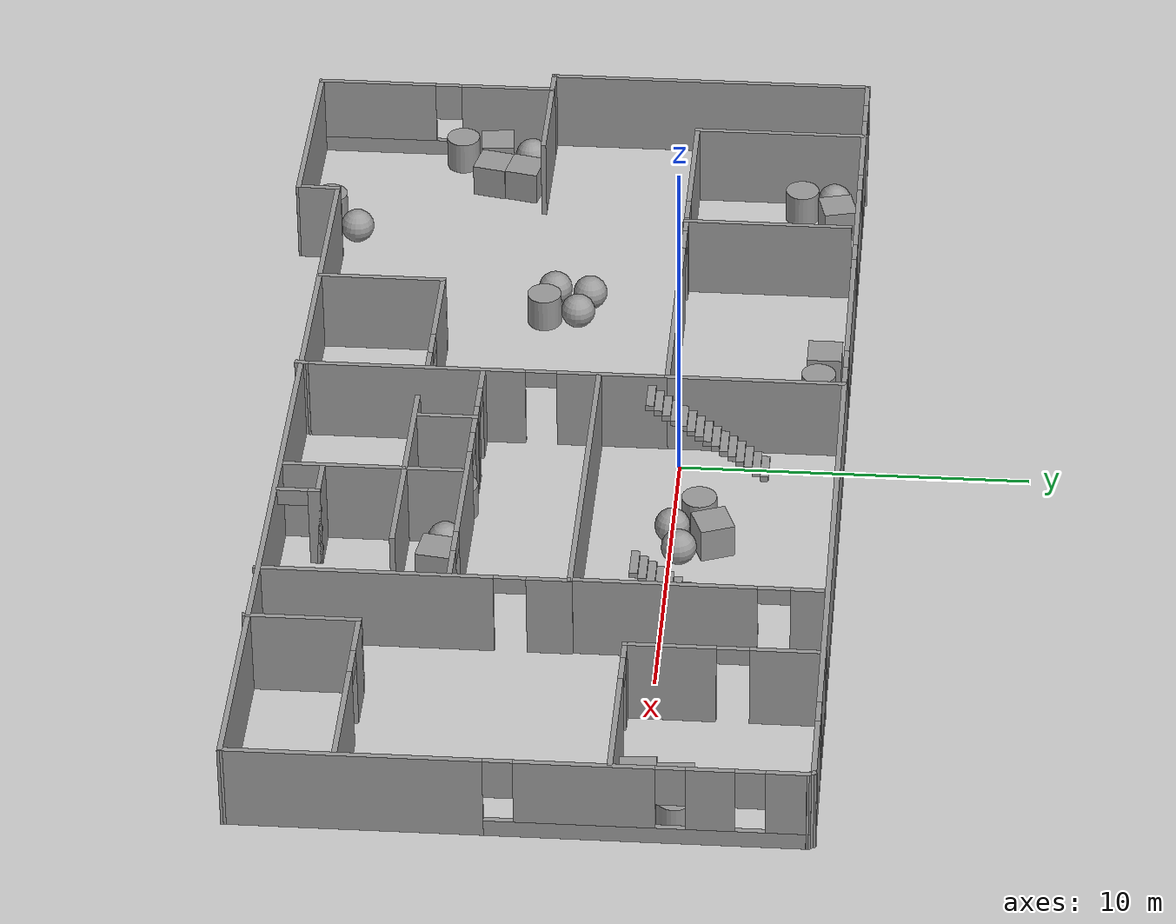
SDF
<sdf version="1.7">
 <world name="default">
  <light name="sun" type="directional">
   <pose>0 0 10 0 -0 0</pose>
   <diffuse>0.8 0.8 0.8 1</diffuse>
   <specular>0.2 0.2 0.2 1</specular>
   <attenuation>
    <range>1000</range>
    <constant>0.9</constant>
    <linear>0.01</linear>
    <quadratic>0.001</quadratic>
   </attenuation>
   <direction>-0.5 0.1 -0.9</direction>
   <spot><inner_angle>0</inner_angle><outer_angle>0</outer_angle><falloff>0</falloff></spot>
  </light>
  <model name="ground_plane">
   <static>1</static>
   <link name="link">
    <collision name="collision">
     <geometry><plane><normal>0 0 1</normal><size>100 100</size></plane></geometry>
     <surface>
      <contact><collide_bitmask>65535</collide_bitmask></contact>
      <friction><ode><mu>100</mu><mu2>50</mu2></ode></friction>
     </surface>
    </collision>
    <visual name="visual">
     <cast_shadows>0</cast_shadows>
     <geometry><plane><normal>0 0 1</normal><size>100 100</size></plane></geometry>
     <material>
      <script><uri>file://media/materials/scripts/gazebo.material</uri><name>Gazebo/Grey</name></script>
     </material>
    </visual>
   </link>
  </model>
  <gravity>0 0 -9.8</gravity>
  <magnetic_field>6e-06 2.3e-05 -4.2e-05</magnetic_field>
  <atmosphere type="adiabatic"/>
  <physics type="ode">
   <max_step_size>0.001</max_step_size>
   <real_time_factor>1</real_time_factor>
   <real_time_update_rate>1000</real_time_update_rate>
  </physics>
  <scene><ambient>0.4 0.4 0.4 1</ambient><background>0.7 0.7 0.7 1</background><shadows>1</shadows></scene>
  <spherical_coordinates>
   <surface_model>EARTH_WGS84</surface_model>
   <latitude_deg>0</latitude_deg>
   <longitude_deg>0</longitude_deg>
   <elevation>0</elevation>
   <heading_deg>0</heading_deg>
  </spherical_coordinates>
  <model name="Dundler_mifflin">
   <pose>0.014796 -3.72139 0 0 -0 0</pose>
   <link name="Stairs_0">
    <visual name="Stairs_0_Visual_0">
     <pose>-0 6.1696 0.083333 0 -0 0</pose>
     <geometry><box><size>1 0.233333 0.166667</size></box></geometry>
     <material>
      <script><uri>file://media/materials/scripts/gazebo.material</uri><name>Gazebo/Grey</name></script>
      <ambient>1 1 1 1</ambient>
     </material>
     <meta><layer>0</layer></meta>
    </visual>
    <collision name="Stairs_0_Collision_0">
     <geometry><box><size>1 0.233333 0.166667</size></box></geometry>
     <pose>-0 6.1696 0.083333 0 -0 0</pose>
    </collision>
    <visual name="Stairs_0_Visual_1">
     <pose>-0 5.93627 0.25 0 -0 0</pose>
     <geometry><box><size>1 0.233333 0.166667</size></box></geometry>
     <material>
      <script><uri>file://media/materials/scripts/gazebo.material</uri><name>Gazebo/Grey</name></script>
      <ambient>1 1 1 1</ambient>
     </material>
     <meta><layer>0</layer></meta>
    </visual>
    <collision name="Stairs_0_Collision_1">
     <geometry><box><size>1 0.233333 0.166667</size></box></geometry>
     <pose>-0 5.93627 0.25 0 -0 0</pose>
    </collision>
    <visual name="Stairs_0_Visual_2">
     <pose>-0 5.70294 0.416667 0 -0 0</pose>
     <geometry><box><size>1 0.233333 0.166667</size></box></geometry>
     <material>
      <script><uri>file://media/materials/scripts/gazebo.material</uri><name>Gazebo/Grey</name></script>
      <ambient>1 1 1 1</ambient>
     </material>
     <meta><layer>0</layer></meta>
    </visual>
    <collision name="Stairs_0_Collision_2">
     <geometry><box><size>1 0.233333 0.166667</size></box></geometry>
     <pose>-0 5.70294 0.416667 0 -0 0</pose>
    </collision>
    <visual name="Stairs_0_Visual_3">
     <pose>-0 5.4696 0.583333 0 -0 0</pose>
     <geometry><box><size>1 0.233333 0.166667</size></box></geometry>
     <material>
      <script><uri>file://media/materials/scripts/gazebo.material</uri><name>Gazebo/Grey</name></script>
      <ambient>1 1 1 1</ambient>
     </material>
     <meta><layer>0</layer></meta>
    </visual>
    <collision name="Stairs_0_Collision_3">
     <geometry><box><size>1 0.233333 0.166667</size></box></geometry>
     <pose>-0 5.4696 0.583333 0 -0 0</pose>
    </collision>
    <visual name="Stairs_0_Visual_4">
     <pose>-0 5.23627 0.75 0 -0 0</pose>
     <geometry><box><size>1 0.233333 0.166667</size></box></geometry>
     <material>
      <script><uri>file://media/materials/scripts/gazebo.material</uri><name>Gazebo/Grey</name></script>
      <ambient>1 1 1 1</ambient>
     </material>
     <meta><layer>0</layer></meta>
    </visual>
    <collision name="Stairs_0_Collision_4">
     <geometry><box><size>1 0.233333 0.166667</size></box></geometry>
     <pose>-0 5.23627 0.75 0 -0 0</pose>
    </collision>
    <visual name="Stairs_0_Visual_5">
     <pose>-0 5.00293 0.916667 0 -0 0</pose>
     <geometry><box><size>1 0.233333 0.166667</size></box></geometry>
     <material>
      <script><uri>file://media/materials/scripts/gazebo.material</uri><name>Gazebo/Grey</name></script>
      <ambient>1 1 1 1</ambient>
     </material>
     <meta><layer>0</layer></meta>
    </visual>
    <collision name="Stairs_0_Collision_5">
     <geometry><box><size>1 0.233333 0.166667</size></box></geometry>
     <pose>-0 5.00293 0.916667 0 -0 0</pose>
    </collision>
    <visual name="Stairs_0_Visual_6">
     <pose>-0 4.7696 1.08333 0 -0 0</pose>
     <geometry><box><size>1 0.233333 0.166667</size></box></geometry>
     <material>
      <script><uri>file://media/materials/scripts/gazebo.material</uri><name>Gazebo/Grey</name></script>
      <ambient>1 1 1 1</ambient>
     </material>
     <meta><layer>0</layer></meta>
    </visual>
    <collision name="Stairs_0_Collision_6">
     <geometry><box><size>1 0.233333 0.166667</size></box></geometry>
     <pose>-0 4.7696 1.08333 0 -0 0</pose>
    </collision>
    <visual name="Stairs_0_Visual_7">
     <pose>-0 4.53627 1.25 0 -0 0</pose>
     <geometry><box><size>1 0.233333 0.166667</size></box></geometry>
     <material>
      <script><uri>file://media/materials/scripts/gazebo.material</uri><name>Gazebo/Grey</name></script>
      <ambient>1 1 1 1</ambient>
     </material>
     <meta><layer>0</layer></meta>
    </visual>
    <collision name="Stairs_0_Collision_7">
     <geometry><box><size>1 0.233333 0.166667</size></box></geometry>
     <pose>-0 4.53627 1.25 0 -0 0</pose>
    </collision>
    <visual name="Stairs_0_Visual_8">
     <pose>-0 4.30293 1.41667 0 -0 0</pose>
     <geometry><box><size>1 0.233333 0.166667</size></box></geometry>
     <material>
      <script><uri>file://media/materials/scripts/gazebo.material</uri><name>Gazebo/Grey</name></script>
      <ambient>1 1 1 1</ambient>
     </material>
     <meta><layer>0</layer></meta>
    </visual>
    <collision name="Stairs_0_Collision_8">
     <geometry><box><size>1 0.233333 0.166667</size></box></geometry>
     <pose>-0 4.30293 1.41667 0 -0 0</pose>
    </collision>
    <visual name="Stairs_0_Visual_9">
     <pose>-0 4.0696 1.58333 0 -0 0</pose>
     <geometry><box><size>1 0.233333 0.166667</size></box></geometry>
     <material>
      <script><uri>file://media/materials/scripts/gazebo.material</uri><name>Gazebo/Grey</name></script>
      <ambient>1 1 1 1</ambient>
     </material>
     <meta><layer>0</layer></meta>
    </visual>
    <collision name="Stairs_0_Collision_9">
     <geometry><box><size>1 0.233333 0.166667</size></box></geometry>
     <pose>-0 4.0696 1.58333 0 -0 0</pose>
    </collision>
    <visual name="Stairs_0_Visual_10">
     <pose>-0 3.83627 1.75 0 -0 0</pose>
     <geometry><box><size>1 0.233333 0.166667</size></box></geometry>
     <material>
      <script><uri>file://media/materials/scripts/gazebo.material</uri><name>Gazebo/Grey</name></script>
      <ambient>1 1 1 1</ambient>
     </material>
     <meta><layer>0</layer></meta>
    </visual>
    <collision name="Stairs_0_Collision_10">
     <geometry><box><size>1 0.233333 0.166667</size></box></geometry>
     <pose>-0 3.83627 1.75 0 -0 0</pose>
    </collision>
    <visual name="Stairs_0_Visual_11">
     <pose>-0 3.60293 1.91667 0 -0 0</pose>
     <geometry><box><size>1 0.233333 0.166667</size></box></geometry>
     <material>
      <script><uri>file://media/materials/scripts/gazebo.material</uri><name>Gazebo/Grey</name></script>
      <ambient>1 1 1 1</ambient>
     </material>
     <meta><layer>0</layer></meta>
    </visual>
    <collision name="Stairs_0_Collision_11">
     <geometry><box><size>1 0.233333 0.166667</size></box></geometry>
     <pose>-0 3.60293 1.91667 0 -0 0</pose>
    </collision>
    <visual name="Stairs_0_Visual_12">
     <pose>-0 3.3696 2.08333 0 -0 0</pose>
     <geometry><box><size>1 0.233333 0.166667</size></box></geometry>
     <material>
      <script><uri>file://media/materials/scripts/gazebo.material</uri><name>Gazebo/Grey</name></script>
      <ambient>1 1 1 1</ambient>
     </material>
     <meta><layer>0</layer></meta>
    </visual>
    <collision name="Stairs_0_Collision_12">
     <geometry><box><size>1 0.233333 0.166667</size></box></geometry>
     <pose>-0 3.3696 2.08333 0 -0 0</pose>
    </collision>
    <visual name="Stairs_0_Visual_13">
     <pose>-0 3.13627 2.25 0 -0 0</pose>
     <geometry><box><size>1 0.233333 0.166667</size></box></geometry>
     <material>
      <script><uri>file://media/materials/scripts/gazebo.material</uri><name>Gazebo/Grey</name></script>
      <ambient>1 1 1 1</ambient>
     </material>
     <meta><layer>0</layer></meta>
    </visual>
    <collision name="Stairs_0_Collision_13">
     <geometry><box><size>1 0.233333 0.166667</size></box></geometry>
     <pose>-0 3.13627 2.25 0 -0 0</pose>
    </collision>
    <visual name="Stairs_0_Visual_14">
     <pose>-0 2.90293 2.41667 0 -0 0</pose>
     <geometry><box><size>1 0.233333 0.166667</size></box></geometry>
     <material>
      <script><uri>file://media/materials/scripts/gazebo.material</uri><name>Gazebo/Grey</name></script>
      <ambient>1 1 1 1</ambient>
     </material>
     <meta><layer>0</layer></meta>
    </visual>
    <collision name="Stairs_0_Collision_14">
     <geometry><box><size>1 0.233333 0.166667</size></box></geometry>
     <pose>-0 2.90293 2.41667 0 -0 0</pose>
    </collision>
   </link>
   <link name="Stairs_1">
    <visual name="Stairs_1_Visual_0">
     <pose>7.80793 6.29097 0.083333 0 -0 0</pose>
     <geometry><box><size>1 0.233333 0.166667</size></box></geometry>
     <material>
      <script><uri>file://media/materials/scripts/gazebo.material</uri><name>Gazebo/Grey</name></script>
      <ambient>1 1 1 1</ambient>
     </material>
     <meta><layer>0</layer></meta>
    </visual>
    <collision name="Stairs_1_Collision_0">
     <geometry><box><size>1 0.233333 0.166667</size></box></geometry>
     <pose>7.80793 6.29097 0.083333 0 -0 0</pose>
    </collision>
    <visual name="Stairs_1_Visual_1">
     <pose>7.80793 6.05764 0.25 0 -0 0</pose>
     <geometry><box><size>1 0.233333 0.166667</size></box></geometry>
     <material>
      <script><uri>file://media/materials/scripts/gazebo.material</uri><name>Gazebo/Grey</name></script>
      <ambient>1 1 1 1</ambient>
     </material>
     <meta><layer>0</layer></meta>
    </visual>
    <collision name="Stairs_1_Collision_1">
     <geometry><box><size>1 0.233333 0.166667</size></box></geometry>
     <pose>7.80793 6.05764 0.25 0 -0 0</pose>
    </collision>
    <visual name="Stairs_1_Visual_2">
     <pose>7.80793 5.8243 0.416667 0 -0 0</pose>
     <geometry><box><size>1 0.233333 0.166667</size></box></geometry>
     <material>
      <script><uri>file://media/materials/scripts/gazebo.material</uri><name>Gazebo/Grey</name></script>
      <ambient>1 1 1 1</ambient>
     </material>
     <meta><layer>0</layer></meta>
    </visual>
    <collision name="Stairs_1_Collision_2">
     <geometry><box><size>1 0.233333 0.166667</size></box></geometry>
     <pose>7.80793 5.8243 0.416667 0 -0 0</pose>
    </collision>
    <visual name="Stairs_1_Visual_3">
     <pose>7.80793 5.59097 0.583333 0 -0 0</pose>
     <geometry><box><size>1 0.233333 0.166667</size></box></geometry>
     <material>
      <script><uri>file://media/materials/scripts/gazebo.material</uri><name>Gazebo/Grey</name></script>
      <ambient>1 1 1 1</ambient>
     </material>
     <meta><layer>0</layer></meta>
    </visual>
    <collision name="Stairs_1_Collision_3">
     <geometry><box><size>1 0.233333 0.166667</size></box></geometry>
     <pose>7.80793 5.59097 0.583333 0 -0 0</pose>
    </collision>
    <visual name="Stairs_1_Visual_4">
     <pose>7.80793 5.35764 0.75 0 -0 0</pose>
     <geometry><box><size>1 0.233333 0.166667</size></box></geometry>
     <material>
      <script><uri>file://media/materials/scripts/gazebo.material</uri><name>Gazebo/Grey</name></script>
      <ambient>1 1 1 1</ambient>
     </material>
     <meta><layer>0</layer></meta>
    </visual>
    <collision name="Stairs_1_Collision_4">
     <geometry><box><size>1 0.233333 0.166667</size></box></geometry>
     <pose>7.80793 5.35764 0.75 0 -0 0</pose>
    </collision>
    <visual name="Stairs_1_Visual_5">
     <pose>7.80793 5.1243 0.916667 0 -0 0</pose>
     <geometry><box><size>1 0.233333 0.166667</size></box></geometry>
     <material>
      <script><uri>file://media/materials/scripts/gazebo.material</uri><name>Gazebo/Grey</name></script>
      <ambient>1 1 1 1</ambient>
     </material>
     <meta><layer>0</layer></meta>
    </visual>
    <collision name="Stairs_1_Collision_5">
     <geometry><box><size>1 0.233333 0.166667</size></box></geometry>
     <pose>7.80793 5.1243 0.916667 0 -0 0</pose>
    </collision>
    <visual name="Stairs_1_Visual_6">
     <pose>7.80793 4.89097 1.08333 0 -0 0</pose>
     <geometry><box><size>1 0.233333 0.166667</size></box></geometry>
     <material>
      <script><uri>file://media/materials/scripts/gazebo.material</uri><name>Gazebo/Grey</name></script>
      <ambient>1 1 1 1</ambient>
     </material>
     <meta><layer>0</layer></meta>
    </visual>
    <collision name="Stairs_1_Collision_6">
     <geometry><box><size>1 0.233333 0.166667</size></box></geometry>
     <pose>7.80793 4.89097 1.08333 0 -0 0</pose>
    </collision>
    <visual name="Stairs_1_Visual_7">
     <pose>7.80793 4.65763 1.25 0 -0 0</pose>
     <geometry><box><size>1 0.233333 0.166667</size></box></geometry>
     <material>
      <script><uri>file://media/materials/scripts/gazebo.material</uri><name>Gazebo/Grey</name></script>
      <ambient>1 1 1 1</ambient>
     </material>
     <meta><layer>0</layer></meta>
    </visual>
    <collision name="Stairs_1_Collision_7">
     <geometry><box><size>1 0.233333 0.166667</size></box></geometry>
     <pose>7.80793 4.65763 1.25 0 -0 0</pose>
    </collision>
    <visual name="Stairs_1_Visual_8">
     <pose>7.80793 4.4243 1.41667 0 -0 0</pose>
     <geometry><box><size>1 0.233333 0.166667</size></box></geometry>
     <material>
      <script><uri>file://media/materials/scripts/gazebo.material</uri><name>Gazebo/Grey</name></script>
      <ambient>1 1 1 1</ambient>
     </material>
     <meta><layer>0</layer></meta>
    </visual>
    <collision name="Stairs_1_Collision_8">
     <geometry><box><size>1 0.233333 0.166667</size></box></geometry>
     <pose>7.80793 4.4243 1.41667 0 -0 0</pose>
    </collision>
    <visual name="Stairs_1_Visual_9">
     <pose>7.80793 4.19097 1.58333 0 -0 0</pose>
     <geometry><box><size>1 0.233333 0.166667</size></box></geometry>
     <material>
      <script><uri>file://media/materials/scripts/gazebo.material</uri><name>Gazebo/Grey</name></script>
      <ambient>1 1 1 1</ambient>
     </material>
     <meta><layer>0</layer></meta>
    </visual>
    <collision name="Stairs_1_Collision_9">
     <geometry><box><size>1 0.233333 0.166667</size></box></geometry>
     <pose>7.80793 4.19097 1.58333 0 -0 0</pose>
    </collision>
    <visual name="Stairs_1_Visual_10">
     <pose>7.80793 3.95763 1.75 0 -0 0</pose>
     <geometry><box><size>1 0.233333 0.166667</size></box></geometry>
     <material>
      <script><uri>file://media/materials/scripts/gazebo.material</uri><name>Gazebo/Grey</name></script>
      <ambient>1 1 1 1</ambient>
     </material>
     <meta><layer>0</layer></meta>
    </visual>
    <collision name="Stairs_1_Collision_10">
     <geometry><box><size>1 0.233333 0.166667</size></box></geometry>
     <pose>7.80793 3.95763 1.75 0 -0 0</pose>
    </collision>
    <visual name="Stairs_1_Visual_11">
     <pose>7.80793 3.7243 1.91667 0 -0 0</pose>
     <geometry><box><size>1 0.233333 0.166667</size></box></geometry>
     <material>
      <script><uri>file://media/materials/scripts/gazebo.material</uri><name>Gazebo/Grey</name></script>
      <ambient>1 1 1 1</ambient>
     </material>
     <meta><layer>0</layer></meta>
    </visual>
    <collision name="Stairs_1_Collision_11">
     <geometry><box><size>1 0.233333 0.166667</size></box></geometry>
     <pose>7.80793 3.7243 1.91667 0 -0 0</pose>
    </collision>
    <visual name="Stairs_1_Visual_12">
     <pose>7.80793 3.49097 2.08333 0 -0 0</pose>
     <geometry><box><size>1 0.233333 0.166667</size></box></geometry>
     <material>
      <script><uri>file://media/materials/scripts/gazebo.material</uri><name>Gazebo/Grey</name></script>
      <ambient>1 1 1 1</ambient>
     </material>
     <meta><layer>0</layer></meta>
    </visual>
    <collision name="Stairs_1_Collision_12">
     <geometry><box><size>1 0.233333 0.166667</size></box></geometry>
     <pose>7.80793 3.49097 2.08333 0 -0 0</pose>
    </collision>
    <visual name="Stairs_1_Visual_13">
     <pose>7.80793 3.25764 2.25 0 -0 0</pose>
     <geometry><box><size>1 0.233333 0.166667</size></box></geometry>
     <material>
      <script><uri>file://media/materials/scripts/gazebo.material</uri><name>Gazebo/Grey</name></script>
      <ambient>1 1 1 1</ambient>
     </material>
     <meta><layer>0</layer></meta>
    </visual>
    <collision name="Stairs_1_Collision_13">
     <geometry><box><size>1 0.233333 0.166667</size></box></geometry>
     <pose>7.80793 3.25764 2.25 0 -0 0</pose>
    </collision>
    <visual name="Stairs_1_Visual_14">
     <pose>7.80793 3.0243 2.41667 0 -0 0</pose>
     <geometry><box><size>1 0.233333 0.166667</size></box></geometry>
     <material>
      <script><uri>file://media/materials/scripts/gazebo.material</uri><name>Gazebo/Grey</name></script>
      <ambient>1 1 1 1</ambient>
     </material>
     <meta><layer>0</layer></meta>
    </visual>
    <collision name="Stairs_1_Collision_14">
     <geometry><box><size>1 0.233333 0.166667</size></box></geometry>
     <pose>7.80793 3.0243 2.41667 0 -0 0</pose>
    </collision>
   </link>
   <link name="Wall_0">
    <collision name="Wall_0_Collision">
     <geometry><box><size>9.73708 0.15 2.5</size></box></geometry>
     <pose>0 0 1.25 0 -0 0</pose>
    </collision>
    <visual name="Wall_0_Visual">
     <pose>0 0 1.25 0 -0 0</pose>
     <geometry><box><size>9.73708 0.15 2.5</size></box></geometry>
     <material>
      <script><uri>file://media/materials/scripts/gazebo.material</uri><name>Gazebo/Grey</name></script>
      <ambient>1 1 1 1</ambient>
     </material>
     <meta><layer>0</layer></meta>
    </visual>
    <pose>-16.6238 3.54458 0 0 -0 -1.56939</pose>
   </link>
   <link name="Wall_1">
    <collision name="Wall_1_Collision">
     <geometry><box><size>0.906952 0.15 2.5</size></box></geometry>
     <pose>0 0 1.25 0 -0 0</pose>
    </collision>
    <visual name="Wall_1_Visual">
     <pose>0 0 1.25 0 -0 0</pose>
     <geometry><box><size>0.906952 0.15 2.5</size></box></geometry>
     <material>
      <script><uri>file://media/materials/scripts/gazebo.material</uri><name>Gazebo/Grey</name></script>
      <ambient>1 1 1 1</ambient>
     </material>
     <meta><layer>0</layer></meta>
    </visual>
    <pose>-16.2386 -1.29532 0 0 -0 0</pose>
   </link>
   <link name="Wall_10">
    <collision name="Wall_10_Collision">
     <geometry><box><size>5.25 0.15 2.5</size></box></geometry>
     <pose>0 0 1.25 0 -0 0</pose>
    </collision>
    <visual name="Wall_10_Visual">
     <pose>0 0 1.25 0 -0 0</pose>
     <geometry><box><size>5.25 0.15 2.5</size></box></geometry>
     <material>
      <script><uri>file://media/materials/scripts/gazebo.material</uri><name>Gazebo/Grey</name></script>
      <ambient>1 1 1 1</ambient>
     </material>
     <meta><layer>0</layer></meta>
    </visual>
    <pose>-13.8957 5.8475 0 0 -0 -1.5708</pose>
   </link>
   <link name="Wall_11">
    <pose>-7.43051 3.2975 0 0 -0 0</pose>
    <visual name="Wall_11_Visual_0">
     <pose>-4.55815 0 1.25 0 -0 0</pose>
     <geometry><box><size>3.96416 0.15 2.5</size></box></geometry>
     <material>
      <script><uri>file://media/materials/scripts/gazebo.material</uri><name>Gazebo/Grey</name></script>
      <ambient>1 1 1 1</ambient>
     </material>
     <meta><layer>0</layer></meta>
    </visual>
    <collision name="Wall_11_Collision_0">
     <geometry><box><size>3.96416 0.15 2.5</size></box></geometry>
     <pose>-4.55815 0 1.25 0 -0 0</pose>
    </collision>
    <visual name="Wall_11_Visual_1">
     <pose>-1.33225 0 1.25 0 -0 0</pose>
     <geometry><box><size>0.687646 0.15 2.5</size></box></geometry>
     <material>
      <script><uri>file://media/materials/scripts/gazebo.material</uri><name>Gazebo/Grey</name></script>
      <ambient>1 1 1 1</ambient>
     </material>
     <meta><layer>0</layer></meta>
    </visual>
    <collision name="Wall_11_Collision_1">
     <geometry><box><size>0.687646 0.15 2.5</size></box></geometry>
     <pose>-1.33225 0 1.25 0 -0 0</pose>
    </collision>
    <visual name="Wall_11_Visual_2">
     <pose>3.2259 0 1.25 0 -0 0</pose>
     <geometry><box><size>6.62865 0.15 2.5</size></box></geometry>
     <material>
      <script><uri>file://media/materials/scripts/gazebo.material</uri><name>Gazebo/Grey</name></script>
      <ambient>1 1 1 1</ambient>
     </material>
     <meta><layer>0</layer></meta>
    </visual>
    <collision name="Wall_11_Collision_2">
     <geometry><box><size>6.62865 0.15 2.5</size></box></geometry>
     <pose>3.2259 0 1.25 0 -0 0</pose>
    </collision>
    <visual name="Wall_11_Visual_3">
     <pose>-2.12607 0 2.25 0 -0 0</pose>
     <geometry><box><size>0.9 0.15 0.5</size></box></geometry>
     <material>
      <script><uri>file://media/materials/scripts/gazebo.material</uri><name>Gazebo/Grey</name></script>
      <ambient>1 1 1 1</ambient>
     </material>
     <meta><layer>0</layer></meta>
    </visual>
    <collision name="Wall_11_Collision_3">
     <geometry><box><size>0.9 0.15 0.5</size></box></geometry>
     <pose>-2.12607 0 2.25 0 -0 0</pose>
    </collision>
    <visual name="Wall_11_Visual_4">
     <pose>-0.538423 0 2.25 0 -0 0</pose>
     <geometry><box><size>0.9 0.15 0.5</size></box></geometry>
     <material>
      <script><uri>file://media/materials/scripts/gazebo.material</uri><name>Gazebo/Grey</name></script>
      <ambient>1 1 1 1</ambient>
     </material>
     <meta><layer>0</layer></meta>
    </visual>
    <collision name="Wall_11_Collision_4">
     <geometry><box><size>0.9 0.15 0.5</size></box></geometry>
     <pose>-0.538423 0 2.25 0 -0 0</pose>
    </collision>
   </link>
   <link name="Wall_12">
    <pose>-0.955224 -1.88756 0 0 -0 -1.56886</pose>
    <visual name="Wall_12_Visual_0">
     <pose>-3.63589 0 1.25 0 -0 0</pose>
     <geometry><box><size>3.24835 0.15 2.5</size></box></geometry>
     <material>
      <script><uri>file://media/materials/scripts/gazebo.material</uri><name>Gazebo/Grey</name></script>
      <ambient>1 1 1 1</ambient>
     </material>
     <meta><layer>0</layer></meta>
    </visual>
    <collision name="Wall_12_Collision_0">
     <geometry><box><size>3.24835 0.15 2.5</size></box></geometry>
     <pose>-3.63589 0 1.25 0 -0 0</pose>
    </collision>
    <visual name="Wall_12_Visual_1">
     <pose>2.07418 0 1.25 0 -0 0</pose>
     <geometry><box><size>6.37178 0.15 2.5</size></box></geometry>
     <material>
      <script><uri>file://media/materials/scripts/gazebo.material</uri><name>Gazebo/Grey</name></script>
      <ambient>1 1 1 1</ambient>
     </material>
     <meta><layer>0</layer></meta>
    </visual>
    <collision name="Wall_12_Collision_1">
     <geometry><box><size>6.37178 0.15 2.5</size></box></geometry>
     <pose>2.07418 0 1.25 0 -0 0</pose>
    </collision>
    <visual name="Wall_12_Visual_2">
     <pose>-1.56171 0 2.25 0 -0 0</pose>
     <geometry><box><size>0.9 0.15 0.5</size></box></geometry>
     <material>
      <script><uri>file://media/materials/scripts/gazebo.material</uri><name>Gazebo/Grey</name></script>
      <ambient>1 1 1 1</ambient>
     </material>
     <meta><layer>0</layer></meta>
    </visual>
    <collision name="Wall_12_Collision_2">
     <geometry><box><size>0.9 0.15 0.5</size></box></geometry>
     <pose>-1.56171 0 2.25 0 -0 0</pose>
    </collision>
   </link>
   <link name="Wall_14">
    <collision name="Wall_14_Collision">
     <geometry><box><size>0.402154 0.15 2.5</size></box></geometry>
     <pose>0 0 1.25 0 -0 0</pose>
    </collision>
    <visual name="Wall_14_Visual">
     <pose>0 0 1.25 0 -0 0</pose>
     <geometry><box><size>0.402154 0.15 2.5</size></box></geometry>
     <material>
      <script><uri>file://media/materials/scripts/gazebo.material</uri><name>Gazebo/Grey</name></script>
      <ambient>1 1 1 1</ambient>
     </material>
     <meta><layer>0</layer></meta>
    </visual>
    <pose>-0.960057 -7.19781 0 0 -0 1.45242</pose>
   </link>
   <link name="Wall_16">
    <collision name="Wall_16_Collision">
     <geometry><box><size>9.72356 0.15 2.5</size></box></geometry>
     <pose>0 0 1.25 0 -0 0</pose>
    </collision>
    <visual name="Wall_16_Visual">
     <pose>0 0 1.25 0 -0 0</pose>
     <geometry><box><size>9.72356 0.15 2.5</size></box></geometry>
     <material>
      <script><uri>file://media/materials/scripts/gazebo.material</uri><name>Gazebo/Grey</name></script>
      <ambient>1 1 1 1</ambient>
     </material>
     <meta><layer>0</layer></meta>
    </visual>
    <pose>3.91536 1.33297 0 0 -0 -0.001938</pose>
   </link>
   <link name="Wall_17">
    <pose>8.71536 4.75797 0 0 -0 1.56694</pose>
    <visual name="Wall_17_Visual_0">
     <pose>-0.909005 0 1.25 0 -0 0</pose>
     <geometry><box><size>5.20056 0.15 2.5</size></box></geometry>
     <material>
      <script><uri>file://media/materials/scripts/gazebo.material</uri><name>Gazebo/Grey</name></script>
      <ambient>1 1 1 1</ambient>
     </material>
     <meta><layer>0</layer></meta>
    </visual>
    <collision name="Wall_17_Collision_0">
     <geometry><box><size>5.20056 0.15 2.5</size></box></geometry>
     <pose>-0.909005 0 1.25 0 -0 0</pose>
    </collision>
    <visual name="Wall_17_Visual_1">
     <pose>3.05028 0 1.25 0 -0 0</pose>
     <geometry><box><size>0.91801 0.15 2.5</size></box></geometry>
     <material>
      <script><uri>file://media/materials/scripts/gazebo.material</uri><name>Gazebo/Grey</name></script>
      <ambient>1 1 1 1</ambient>
     </material>
     <meta><layer>0</layer></meta>
    </visual>
    <collision name="Wall_17_Collision_1">
     <geometry><box><size>0.91801 0.15 2.5</size></box></geometry>
     <pose>3.05028 0 1.25 0 -0 0</pose>
    </collision>
    <visual name="Wall_17_Visual_2">
     <pose>2.14127 0 2.25 0 -0 0</pose>
     <geometry><box><size>0.9 0.15 0.5</size></box></geometry>
     <material>
      <script><uri>file://media/materials/scripts/gazebo.material</uri><name>Gazebo/Grey</name></script>
      <ambient>1 1 1 1</ambient>
     </material>
     <meta><layer>0</layer></meta>
    </visual>
    <collision name="Wall_17_Collision_2">
     <geometry><box><size>0.9 0.15 0.5</size></box></geometry>
     <pose>2.14127 0 2.25 0 -0 0</pose>
    </collision>
   </link>
   <link name="Wall_19">
    <pose>8.74259 -2.97631 0 0 -0 -1.5708</pose>
    <visual name="Wall_19_Visual_0">
     <pose>-3.73996 0 1.25 0 -0 0</pose>
     <geometry><box><size>1.27008 0.15 2.5</size></box></geometry>
     <material>
      <script><uri>file://media/materials/scripts/gazebo.material</uri><name>Gazebo/Grey</name></script>
      <ambient>1 1 1 1</ambient>
     </material>
     <meta><layer>0</layer></meta>
    </visual>
    <collision name="Wall_19_Collision_0">
     <geometry><box><size>1.27008 0.15 2.5</size></box></geometry>
     <pose>-3.73996 0 1.25 0 -0 0</pose>
    </collision>
    <visual name="Wall_19_Visual_1">
     <pose>1.08504 0 1.25 0 -0 0</pose>
     <geometry><box><size>6.57992 0.15 2.5</size></box></geometry>
     <material>
      <script><uri>file://media/materials/scripts/gazebo.material</uri><name>Gazebo/Grey</name></script>
      <ambient>1 1 1 1</ambient>
     </material>
     <meta><layer>0</layer></meta>
    </visual>
    <collision name="Wall_19_Collision_1">
     <geometry><box><size>6.57992 0.15 2.5</size></box></geometry>
     <pose>1.08504 0 1.25 0 -0 0</pose>
    </collision>
    <visual name="Wall_19_Visual_2">
     <pose>-2.65492 0 2.25 0 -0 0</pose>
     <geometry><box><size>0.9 0.15 0.5</size></box></geometry>
     <material>
      <script><uri>file://media/materials/scripts/gazebo.material</uri><name>Gazebo/Grey</name></script>
      <ambient>1 1 1 1</ambient>
     </material>
     <meta><layer>0</layer></meta>
    </visual>
    <collision name="Wall_19_Collision_2">
     <geometry><box><size>0.9 0.15 0.5</size></box></geometry>
     <pose>-2.65492 0 2.25 0 -0 0</pose>
    </collision>
   </link>
   <link name="Wall_2">
    <pose>-15.8601 -4.84532 0 0 -0 -1.5708</pose>
    <visual name="Wall_2_Visual_0">
     <pose>-2.1925 0 1.25 0 -0 0</pose>
     <geometry><box><size>2.865 0.15 2.5</size></box></geometry>
     <material>
      <script><uri>file://media/materials/scripts/gazebo.material</uri><name>Gazebo/Grey</name></script>
      <ambient>1 1 1 1</ambient>
     </material>
     <meta><layer>0</layer></meta>
    </visual>
    <collision name="Wall_2_Collision_0">
     <geometry><box><size>2.865 0.15 2.5</size></box></geometry>
     <pose>-2.1925 0 1.25 0 -0 0</pose>
    </collision>
    <visual name="Wall_2_Visual_1">
     <pose>1.4325 0 0.25 0 -0 0</pose>
     <geometry><box><size>4.385 0.15 0.5</size></box></geometry>
     <material>
      <script><uri>file://media/materials/scripts/gazebo.material</uri><name>Gazebo/Grey</name></script>
      <ambient>1 1 1 1</ambient>
     </material>
     <meta><layer>0</layer></meta>
    </visual>
    <collision name="Wall_2_Collision_1">
     <geometry><box><size>4.385 0.15 0.5</size></box></geometry>
     <pose>1.4325 0 0.25 0 -0 0</pose>
    </collision>
    <visual name="Wall_2_Visual_2">
     <pose>1.8325 0 1.5 0 -0 0</pose>
     <geometry><box><size>3.585 0.15 2</size></box></geometry>
     <material>
      <script><uri>file://media/materials/scripts/gazebo.material</uri><name>Gazebo/Grey</name></script>
      <ambient>1 1 1 1</ambient>
     </material>
     <meta><layer>0</layer></meta>
    </visual>
    <collision name="Wall_2_Collision_2">
     <geometry><box><size>3.585 0.15 2</size></box></geometry>
     <pose>1.8325 0 1.5 0 -0 0</pose>
    </collision>
    <visual name="Wall_2_Visual_3">
     <pose>-0.359998 0 1.9 0 -0 0</pose>
     <geometry><box><size>0.8 0.15 1.2</size></box></geometry>
     <material>
      <script><uri>file://media/materials/scripts/gazebo.material</uri><name>Gazebo/Grey</name></script>
      <ambient>1 1 1 1</ambient>
     </material>
     <meta><layer>0</layer></meta>
    </visual>
    <collision name="Wall_2_Collision_3">
     <geometry><box><size>0.8 0.15 1.2</size></box></geometry>
     <pose>-0.359998 0 1.9 0 -0 0</pose>
    </collision>
   </link>
   <link name="Wall_21">
    <pose>3.86393 -1.97588 0 0 -0 0</pose>
    <visual name="Wall_21_Visual_0">
     <pose>-4.38876 0 1.25 0 -0 0</pose>
     <geometry><box><size>0.972488 0.15 2.5</size></box></geometry>
     <material>
      <script><uri>file://media/materials/scripts/gazebo.material</uri><name>Gazebo/Grey</name></script>
      <ambient>1 1 1 1</ambient>
     </material>
     <meta><layer>0</layer></meta>
    </visual>
    <collision name="Wall_21_Collision_0">
     <geometry><box><size>0.972488 0.15 2.5</size></box></geometry>
     <pose>-4.38876 0 1.25 0 -0 0</pose>
    </collision>
    <visual name="Wall_21_Visual_1">
     <pose>-2.36833 0 1.25 0 -0 0</pose>
     <geometry><box><size>1.26836 0.15 2.5</size></box></geometry>
     <material>
      <script><uri>file://media/materials/scripts/gazebo.material</uri><name>Gazebo/Grey</name></script>
      <ambient>1 1 1 1</ambient>
     </material>
     <meta><layer>0</layer></meta>
    </visual>
    <collision name="Wall_21_Collision_1">
     <geometry><box><size>1.26836 0.15 2.5</size></box></geometry>
     <pose>-2.36833 0 1.25 0 -0 0</pose>
    </collision>
    <visual name="Wall_21_Visual_2">
     <pose>1.02891 0 1.25 0 -0 0</pose>
     <geometry><box><size>3.72612 0.15 2.5</size></box></geometry>
     <material>
      <script><uri>file://media/materials/scripts/gazebo.material</uri><name>Gazebo/Grey</name></script>
      <ambient>1 1 1 1</ambient>
     </material>
     <meta><layer>0</layer></meta>
    </visual>
    <collision name="Wall_21_Collision_2">
     <geometry><box><size>3.72612 0.15 2.5</size></box></geometry>
     <pose>1.02891 0 1.25 0 -0 0</pose>
    </collision>
    <visual name="Wall_21_Visual_3">
     <pose>4.33349 0 1.25 0 -0 0</pose>
     <geometry><box><size>1.08303 0.15 2.5</size></box></geometry>
     <material>
      <script><uri>file://media/materials/scripts/gazebo.material</uri><name>Gazebo/Grey</name></script>
      <ambient>1 1 1 1</ambient>
     </material>
     <meta><layer>0</layer></meta>
    </visual>
    <collision name="Wall_21_Collision_3">
     <geometry><box><size>1.08303 0.15 2.5</size></box></geometry>
     <pose>4.33349 0 1.25 0 -0 0</pose>
    </collision>
    <visual name="Wall_21_Visual_4">
     <pose>-3.45251 0 2.25 0 -0 0</pose>
     <geometry><box><size>0.9 0.15 0.5</size></box></geometry>
     <material>
      <script><uri>file://media/materials/scripts/gazebo.material</uri><name>Gazebo/Grey</name></script>
      <ambient>1 1 1 1</ambient>
     </material>
     <meta><layer>0</layer></meta>
    </visual>
    <collision name="Wall_21_Collision_4">
     <geometry><box><size>0.9 0.15 0.5</size></box></geometry>
     <pose>-3.45251 0 2.25 0 -0 0</pose>
    </collision>
    <visual name="Wall_21_Visual_5">
     <pose>-1.28415 0 2.25 0 -0 0</pose>
     <geometry><box><size>0.9 0.15 0.5</size></box></geometry>
     <material>
      <script><uri>file://media/materials/scripts/gazebo.material</uri><name>Gazebo/Grey</name></script>
      <ambient>1 1 1 1</ambient>
     </material>
     <meta><layer>0</layer></meta>
    </visual>
    <collision name="Wall_21_Collision_5">
     <geometry><box><size>0.9 0.15 0.5</size></box></geometry>
     <pose>-1.28415 0 2.25 0 -0 0</pose>
    </collision>
    <visual name="Wall_21_Visual_6">
     <pose>3.34197 0 2.25 0 -0 0</pose>
     <geometry><box><size>0.9 0.15 0.5</size></box></geometry>
     <material>
      <script><uri>file://media/materials/scripts/gazebo.material</uri><name>Gazebo/Grey</name></script>
      <ambient>1 1 1 1</ambient>
     </material>
     <meta><layer>0</layer></meta>
    </visual>
    <collision name="Wall_21_Collision_6">
     <geometry><box><size>0.9 0.15 0.5</size></box></geometry>
     <pose>3.34197 0 2.25 0 -0 0</pose>
    </collision>
   </link>
   <link name="Wall_23">
    <collision name="Wall_23_Collision">
     <geometry><box><size>5.25 0.15 2.5</size></box></geometry>
     <pose>0 0 1.25 0 -0 0</pose>
    </collision>
    <visual name="Wall_23_Visual">
     <pose>0 0 1.25 0 -0 0</pose>
     <geometry><box><size>5.25 0.15 2.5</size></box></geometry>
     <material>
      <script><uri>file://media/materials/scripts/gazebo.material</uri><name>Gazebo/Grey</name></script>
      <ambient>1 1 1 1</ambient>
     </material>
     <meta><layer>0</layer></meta>
    </visual>
    <pose>3.92136 -4.66467 0 0 -0 -1.5708</pose>
   </link>
   <link name="Wall_25">
    <collision name="Wall_25_Collision">
     <geometry><box><size>6.75 0.15 2.5</size></box></geometry>
     <pose>0 0 1.25 0 -0 0</pose>
    </collision>
    <visual name="Wall_25_Visual">
     <pose>0 0 1.25 0 -0 0</pose>
     <geometry><box><size>6.75 0.15 2.5</size></box></geometry>
     <material>
      <script><uri>file://media/materials/scripts/gazebo.material</uri><name>Gazebo/Grey</name></script>
      <ambient>1 1 1 1</ambient>
     </material>
     <meta><layer>0</layer></meta>
    </visual>
    <pose>3.82116 -3.71068 0 0 -0 0</pose>
   </link>
   <link name="Wall_27">
    <pose>11.4275 5.71132 0 0 -0 -1.5708</pose>
    <visual name="Wall_27_Visual_0">
     <pose>-1.71906 0 1.25 0 -0 0</pose>
     <geometry><box><size>2.06188 0.15 2.5</size></box></geometry>
     <material>
      <script><uri>file://media/materials/scripts/gazebo.material</uri><name>Gazebo/Grey</name></script>
      <ambient>1 1 1 1</ambient>
     </material>
     <meta><layer>0</layer></meta>
    </visual>
    <collision name="Wall_27_Collision_0">
     <geometry><box><size>2.06188 0.15 2.5</size></box></geometry>
     <pose>-1.71906 0 1.25 0 -0 0</pose>
    </collision>
    <visual name="Wall_27_Visual_1">
     <pose>1.48094 0 1.25 0 -0 0</pose>
     <geometry><box><size>2.53812 0.15 2.5</size></box></geometry>
     <material>
      <script><uri>file://media/materials/scripts/gazebo.material</uri><name>Gazebo/Grey</name></script>
      <ambient>1 1 1 1</ambient>
     </material>
     <meta><layer>0</layer></meta>
    </visual>
    <collision name="Wall_27_Collision_1">
     <geometry><box><size>2.53812 0.15 2.5</size></box></geometry>
     <pose>1.48094 0 1.25 0 -0 0</pose>
    </collision>
    <visual name="Wall_27_Visual_2">
     <pose>-0.238121 0 2.25 0 -0 0</pose>
     <geometry><box><size>0.9 0.15 0.5</size></box></geometry>
     <material>
      <script><uri>file://media/materials/scripts/gazebo.material</uri><name>Gazebo/Grey</name></script>
      <ambient>1 1 1 1</ambient>
     </material>
     <meta><layer>0</layer></meta>
    </visual>
    <collision name="Wall_27_Collision_2">
     <geometry><box><size>0.9 0.15 0.5</size></box></geometry>
     <pose>-0.238121 0 2.25 0 -0 0</pose>
    </collision>
   </link>
   <link name="Wall_28">
    <pose>13.9775 3.03632 0 0 -0 0</pose>
    <visual name="Wall_28_Visual_0">
     <pose>-2.28737 0 1.25 0 -0 0</pose>
     <geometry><box><size>0.675255 0.15 2.5</size></box></geometry>
     <material>
      <script><uri>file://media/materials/scripts/gazebo.material</uri><name>Gazebo/Grey</name></script>
      <ambient>1 1 1 1</ambient>
     </material>
     <meta><layer>0</layer></meta>
    </visual>
    <collision name="Wall_28_Collision_0">
     <geometry><box><size>0.675255 0.15 2.5</size></box></geometry>
     <pose>-2.28737 0 1.25 0 -0 0</pose>
    </collision>
    <visual name="Wall_28_Visual_1">
     <pose>0.787627 0 1.25 0 -0 0</pose>
     <geometry><box><size>3.67475 0.15 2.5</size></box></geometry>
     <material>
      <script><uri>file://media/materials/scripts/gazebo.material</uri><name>Gazebo/Grey</name></script>
      <ambient>1 1 1 1</ambient>
     </material>
     <meta><layer>0</layer></meta>
    </visual>
    <collision name="Wall_28_Collision_1">
     <geometry><box><size>3.67475 0.15 2.5</size></box></geometry>
     <pose>0.787627 0 1.25 0 -0 0</pose>
    </collision>
    <visual name="Wall_28_Visual_2">
     <pose>-1.49975 0 2.25 0 -0 0</pose>
     <geometry><box><size>0.9 0.15 0.5</size></box></geometry>
     <material>
      <script><uri>file://media/materials/scripts/gazebo.material</uri><name>Gazebo/Grey</name></script>
      <ambient>1 1 1 1</ambient>
     </material>
     <meta><layer>0</layer></meta>
    </visual>
    <collision name="Wall_28_Collision_2">
     <geometry><box><size>0.9 0.15 0.5</size></box></geometry>
     <pose>-1.49975 0 2.25 0 -0 0</pose>
    </collision>
   </link>
   <link name="Wall_3">
    <collision name="Wall_3_Collision">
     <geometry><box><size>6 0.15 2.5</size></box></geometry>
     <pose>0 0 1.25 0 -0 0</pose>
    </collision>
    <visual name="Wall_3_Visual">
     <pose>0 0 1.25 0 -0 0</pose>
     <geometry><box><size>6 0.15 2.5</size></box></geometry>
     <material>
      <script><uri>file://media/materials/scripts/gazebo.material</uri><name>Gazebo/Grey</name></script>
      <ambient>1 1 1 1</ambient>
     </material>
     <meta><layer>0</layer></meta>
    </visual>
    <pose>-12.9351 -8.39532 0 0 -0 0</pose>
   </link>
   <link name="Wall_30">
    <collision name="Wall_30_Collision">
     <geometry><box><size>5 0.15 2.5</size></box></geometry>
     <pose>0 0 1.25 0 -0 0</pose>
    </collision>
    <visual name="Wall_30_Visual">
     <pose>0 0 1.25 0 -0 0</pose>
     <geometry><box><size>5 0.15 2.5</size></box></geometry>
     <material>
      <script><uri>file://media/materials/scripts/gazebo.material</uri><name>Gazebo/Grey</name></script>
      <ambient>1 1 1 1</ambient>
     </material>
     <meta><layer>0</layer></meta>
    </visual>
    <pose>-8.94957 5.70028 0 0 -0 -1.5708</pose>
   </link>
   <link name="Wall_32">
    <collision name="Wall_32_Collision">
     <geometry><box><size>1.75 0.15 2.5</size></box></geometry>
     <pose>0 0 1.25 0 -0 0</pose>
    </collision>
    <visual name="Wall_32_Visual">
     <pose>0 0 1.25 0 -0 0</pose>
     <geometry><box><size>1.75 0.15 2.5</size></box></geometry>
     <material>
      <script><uri>file://media/materials/scripts/gazebo.material</uri><name>Gazebo/Grey</name></script>
      <ambient>1 1 1 1</ambient>
     </material>
     <meta><layer>0</layer></meta>
    </visual>
    <pose>1.36125 -2.76578 0 0 -0 -1.5708</pose>
   </link>
   <link name="Wall_34">
    <collision name="Wall_34_Collision">
     <geometry><box><size>5.16909 0.15 2.5</size></box></geometry>
     <pose>0 0 1.25 0 -0 0</pose>
    </collision>
    <visual name="Wall_34_Visual">
     <pose>0 0 1.25 0 -0 0</pose>
     <geometry><box><size>5.16909 0.15 2.5</size></box></geometry>
     <material>
      <script><uri>file://media/materials/scripts/gazebo.material</uri><name>Gazebo/Grey</name></script>
      <ambient>1 1 1 1</ambient>
     </material>
     <meta><layer>0</layer></meta>
    </visual>
    <pose>-0.965281 5.80704 0 0 -0 1.5708</pose>
   </link>
   <link name="Wall_37">
    <collision name="Wall_37_Collision">
     <geometry><box><size>3.25 0.15 2.5</size></box></geometry>
     <pose>0 0 1.25 0 -0 0</pose>
    </collision>
    <visual name="Wall_37_Visual">
     <pose>0 0 1.25 0 -0 0</pose>
     <geometry><box><size>3.25 0.15 2.5</size></box></geometry>
     <material>
      <script><uri>file://media/materials/scripts/gazebo.material</uri><name>Gazebo/Grey</name></script>
      <ambient>1 1 1 1</ambient>
     </material>
     <meta><layer>0</layer></meta>
    </visual>
    <pose>-14.3101 -1.29532 0 0 -0 0</pose>
   </link>
   <link name="Wall_4">
    <collision name="Wall_4_Collision">
     <geometry><box><size>1.33091 0.15 2.5</size></box></geometry>
     <pose>0 0 1.25 0 -0 0</pose>
    </collision>
    <visual name="Wall_4_Visual">
     <pose>0 0 1.25 0 -0 0</pose>
     <geometry><box><size>1.33091 0.15 2.5</size></box></geometry>
     <material>
      <script><uri>file://media/materials/scripts/gazebo.material</uri><name>Gazebo/Grey</name></script>
      <ambient>1 1 1 1</ambient>
     </material>
     <meta><layer>0</layer></meta>
    </visual>
    <pose>-9.98985 -7.80487 0 0 -0 1.53655</pose>
   </link>
   <link name="Wall_40">
    <collision name="Wall_40_Collision">
     <geometry><box><size>3.25 0.15 2.5</size></box></geometry>
     <pose>0 0 1.25 0 -0 0</pose>
    </collision>
    <visual name="Wall_40_Visual">
     <pose>0 0 1.25 0 -0 0</pose>
     <geometry><box><size>3.25 0.15 2.5</size></box></geometry>
     <material>
      <script><uri>file://media/materials/scripts/gazebo.material</uri><name>Gazebo/Grey</name></script>
      <ambient>1 1 1 1</ambient>
     </material>
     <meta><layer>0</layer></meta>
    </visual>
    <pose>10.8761 -5.75105 0 0 -0 1.5708</pose>
   </link>
   <link name="Wall_41">
    <pose>13.6761 -4.20105 0 0 -0 0</pose>
    <visual name="Wall_41_Visual_0">
     <pose>-2.15225 0 1.25 0 -0 0</pose>
     <geometry><box><size>1.4455 0.15 2.5</size></box></geometry>
     <material>
      <script><uri>file://media/materials/scripts/gazebo.material</uri><name>Gazebo/Grey</name></script>
      <ambient>1 1 1 1</ambient>
     </material>
     <meta><layer>0</layer></meta>
    </visual>
    <collision name="Wall_41_Collision_0">
     <geometry><box><size>1.4455 0.15 2.5</size></box></geometry>
     <pose>-2.15225 0 1.25 0 -0 0</pose>
    </collision>
    <visual name="Wall_41_Visual_1">
     <pose>1.17275 0 1.25 0 -0 0</pose>
     <geometry><box><size>3.4045 0.15 2.5</size></box></geometry>
     <material>
      <script><uri>file://media/materials/scripts/gazebo.material</uri><name>Gazebo/Grey</name></script>
      <ambient>1 1 1 1</ambient>
     </material>
     <meta><layer>0</layer></meta>
    </visual>
    <collision name="Wall_41_Collision_1">
     <geometry><box><size>3.4045 0.15 2.5</size></box></geometry>
     <pose>1.17275 0 1.25 0 -0 0</pose>
    </collision>
    <visual name="Wall_41_Visual_2">
     <pose>-0.9795 0 2.25 0 -0 0</pose>
     <geometry><box><size>0.9 0.15 0.5</size></box></geometry>
     <material>
      <script><uri>file://media/materials/scripts/gazebo.material</uri><name>Gazebo/Grey</name></script>
      <ambient>1 1 1 1</ambient>
     </material>
     <meta><layer>0</layer></meta>
    </visual>
    <collision name="Wall_41_Collision_2">
     <geometry><box><size>0.9 0.15 0.5</size></box></geometry>
     <pose>-0.9795 0 2.25 0 -0 0</pose>
    </collision>
   </link>
   <link name="Wall_43">
    <collision name="Wall_43_Collision">
     <geometry><box><size>1.25 0.15 2.5</size></box></geometry>
     <pose>0 0 1.25 0 -0 0</pose>
    </collision>
    <visual name="Wall_43_Visual">
     <pose>0 0 1.25 0 -0 0</pose>
     <geometry><box><size>1.25 0.15 2.5</size></box></geometry>
     <material>
      <script><uri>file://media/materials/scripts/gazebo.material</uri><name>Gazebo/Grey</name></script>
      <ambient>1 1 1 1</ambient>
     </material>
     <meta><layer>0</layer></meta>
    </visual>
    <pose>4.58911 -6.00647 0 0 -0 0</pose>
   </link>
   <link name="Wall_44">
    <pose>5.13911 -6.55647 0 0 -0 -1.5708</pose>
    <visual name="Wall_44_Visual_0">
     <pose>-0.4484 0 1.25 0 -0 0</pose>
     <geometry><box><size>0.3532 0.15 2.5</size></box></geometry>
     <material>
      <script><uri>file://media/materials/scripts/gazebo.material</uri><name>Gazebo/Grey</name></script>
      <ambient>1 1 1 1</ambient>
     </material>
     <meta><layer>0</layer></meta>
    </visual>
    <collision name="Wall_44_Collision_0">
     <geometry><box><size>0.3532 0.15 2.5</size></box></geometry>
     <pose>-0.4484 0 1.25 0 -0 0</pose>
    </collision>
    <visual name="Wall_44_Visual_1">
     <pose>0.1766 0 2.25 0 -0 0</pose>
     <geometry><box><size>0.8968 0.15 0.5</size></box></geometry>
     <material>
      <script><uri>file://media/materials/scripts/gazebo.material</uri><name>Gazebo/Grey</name></script>
      <ambient>1 1 1 1</ambient>
     </material>
     <meta><layer>0</layer></meta>
    </visual>
    <collision name="Wall_44_Collision_1">
     <geometry><box><size>0.8968 0.15 0.5</size></box></geometry>
     <pose>0.1766 0 2.25 0 -0 0</pose>
    </collision>
   </link>
   <link name="Wall_46">
    <collision name="Wall_46_Collision">
     <geometry><box><size>3.75 0.15 2.5</size></box></geometry>
     <pose>0 0 1.25 0 -0 0</pose>
    </collision>
    <visual name="Wall_46_Visual">
     <pose>0 0 1.25 0 -0 0</pose>
     <geometry><box><size>3.75 0.15 2.5</size></box></geometry>
     <material>
      <script><uri>file://media/materials/scripts/gazebo.material</uri><name>Gazebo/Grey</name></script>
      <ambient>1 1 1 1</ambient>
     </material>
     <meta><layer>0</layer></meta>
    </visual>
    <pose>-5.38704 -5.37969 0 0 -0 1.5708</pose>
   </link>
   <link name="Wall_47">
    <pose>-3.19181 -3.57969 0 0 -0 0</pose>
    <visual name="Wall_47_Visual_0">
     <pose>-0.839551 0 1.25 0 -0 0</pose>
     <geometry><box><size>2.86154 0.15 2.5</size></box></geometry>
     <material>
      <script><uri>file://media/materials/scripts/gazebo.material</uri><name>Gazebo/Grey</name></script>
      <ambient>1 1 1 1</ambient>
     </material>
     <meta><layer>0</layer></meta>
    </visual>
    <collision name="Wall_47_Collision_0">
     <geometry><box><size>2.86154 0.15 2.5</size></box></geometry>
     <pose>-0.839551 0 1.25 0 -0 0</pose>
    </collision>
    <visual name="Wall_47_Visual_1">
     <pose>1.88077 0 1.25 0 -0 0</pose>
     <geometry><box><size>0.779103 0.15 2.5</size></box></geometry>
     <material>
      <script><uri>file://media/materials/scripts/gazebo.material</uri><name>Gazebo/Grey</name></script>
      <ambient>1 1 1 1</ambient>
     </material>
     <meta><layer>0</layer></meta>
    </visual>
    <collision name="Wall_47_Collision_1">
     <geometry><box><size>0.779103 0.15 2.5</size></box></geometry>
     <pose>1.88077 0 1.25 0 -0 0</pose>
    </collision>
    <visual name="Wall_47_Visual_2">
     <pose>1.04122 0 2.25 0 -0 0</pose>
     <geometry><box><size>0.9 0.15 0.5</size></box></geometry>
     <material>
      <script><uri>file://media/materials/scripts/gazebo.material</uri><name>Gazebo/Grey</name></script>
      <ambient>1 1 1 1</ambient>
     </material>
     <meta><layer>0</layer></meta>
    </visual>
    <collision name="Wall_47_Collision_2">
     <geometry><box><size>0.9 0.15 0.5</size></box></geometry>
     <pose>1.04122 0 2.25 0 -0 0</pose>
    </collision>
   </link>
   <link name="Wall_5">
    <collision name="Wall_5_Collision">
     <geometry><box><size>26.75 0.15 2.5</size></box></geometry>
     <pose>0 0 1.25 0 -0 0</pose>
    </collision>
    <visual name="Wall_5_Visual">
     <pose>0 0 1.25 0 -0 0</pose>
     <geometry><box><size>26.75 0.15 2.5</size></box></geometry>
     <material>
      <script><uri>file://media/materials/scripts/gazebo.material</uri><name>Gazebo/Grey</name></script>
      <ambient>1 1 1 1</ambient>
     </material>
     <meta><layer>0</layer></meta>
    </visual>
    <pose>3.33038 -7.21441 0 0 -0 0</pose>
   </link>
   <link name="Wall_6">
    <pose>16.6077 0.513998 0 0 -0 1.57373</pose>
    <visual name="Wall_6_Visual_0">
     <pose>-4.31589 0 1.25 0 -0 0</pose>
     <geometry><box><size>6.97527 0.15 2.5</size></box></geometry>
     <material>
      <script><uri>file://media/materials/scripts/gazebo.material</uri><name>Gazebo/Grey</name></script>
      <ambient>1 1 1 1</ambient>
     </material>
     <meta><layer>0</layer></meta>
    </visual>
    <collision name="Wall_6_Collision_0">
     <geometry><box><size>6.97527 0.15 2.5</size></box></geometry>
     <pose>-4.31589 0 1.25 0 -0 0</pose>
    </collision>
    <visual name="Wall_6_Visual_1">
     <pose>3.48764 0 0.25 0 -0 0</pose>
     <geometry><box><size>8.63179 0.15 0.5</size></box></geometry>
     <material>
      <script><uri>file://media/materials/scripts/gazebo.material</uri><name>Gazebo/Grey</name></script>
      <ambient>1 1 1 1</ambient>
     </material>
     <meta><layer>0</layer></meta>
    </visual>
    <collision name="Wall_6_Collision_1">
     <geometry><box><size>8.63179 0.15 0.5</size></box></geometry>
     <pose>3.48764 0 0.25 0 -0 0</pose>
    </collision>
    <visual name="Wall_6_Visual_2">
     <pose>1.83749 0 1.5 0 -0 0</pose>
     <geometry><box><size>3.73148 0.15 2</size></box></geometry>
     <material>
      <script><uri>file://media/materials/scripts/gazebo.material</uri><name>Gazebo/Grey</name></script>
      <ambient>1 1 1 1</ambient>
     </material>
     <meta><layer>0</layer></meta>
    </visual>
    <collision name="Wall_6_Collision_2">
     <geometry><box><size>3.73148 0.15 2</size></box></geometry>
     <pose>1.83749 0 1.5 0 -0 0</pose>
    </collision>
    <visual name="Wall_6_Visual_3">
     <pose>5.15477 0 1.5 0 -0 0</pose>
     <geometry><box><size>1.30309 0.15 2</size></box></geometry>
     <material>
      <script><uri>file://media/materials/scripts/gazebo.material</uri><name>Gazebo/Grey</name></script>
      <ambient>1 1 1 1</ambient>
     </material>
     <meta><layer>0</layer></meta>
    </visual>
    <collision name="Wall_6_Collision_3">
     <geometry><box><size>1.30309 0.15 2</size></box></geometry>
     <pose>5.15477 0 1.5 0 -0 0</pose>
    </collision>
    <visual name="Wall_6_Visual_4">
     <pose>7.20492 0 1.5 0 -0 0</pose>
     <geometry><box><size>1.19722 0.15 2</size></box></geometry>
     <material>
      <script><uri>file://media/materials/scripts/gazebo.material</uri><name>Gazebo/Grey</name></script>
      <ambient>1 1 1 1</ambient>
     </material>
     <meta><layer>0</layer></meta>
    </visual>
    <collision name="Wall_6_Collision_4">
     <geometry><box><size>1.19722 0.15 2</size></box></geometry>
     <pose>7.20492 0 1.5 0 -0 0</pose>
    </collision>
    <visual name="Wall_6_Visual_5">
     <pose>-0.428255 0 1.9 0 -0 0</pose>
     <geometry><box><size>0.8 0.15 1.2</size></box></geometry>
     <material>
      <script><uri>file://media/materials/scripts/gazebo.material</uri><name>Gazebo/Grey</name></script>
      <ambient>1 1 1 1</ambient>
     </material>
     <meta><layer>0</layer></meta>
    </visual>
    <collision name="Wall_6_Collision_5">
     <geometry><box><size>0.8 0.15 1.2</size></box></geometry>
     <pose>-0.428255 0 1.9 0 -0 0</pose>
    </collision>
    <visual name="Wall_6_Visual_6">
     <pose>4.10323 0 1.9 0 -0 0</pose>
     <geometry><box><size>0.8 0.15 1.2</size></box></geometry>
     <material>
      <script><uri>file://media/materials/scripts/gazebo.material</uri><name>Gazebo/Grey</name></script>
      <ambient>1 1 1 1</ambient>
     </material>
     <meta><layer>0</layer></meta>
    </visual>
    <collision name="Wall_6_Collision_6">
     <geometry><box><size>0.8 0.15 1.2</size></box></geometry>
     <pose>4.10323 0 1.9 0 -0 0</pose>
    </collision>
    <visual name="Wall_6_Visual_7">
     <pose>6.20631 0 1.9 0 -0 0</pose>
     <geometry><box><size>0.8 0.15 1.2</size></box></geometry>
     <material>
      <script><uri>file://media/materials/scripts/gazebo.material</uri><name>Gazebo/Grey</name></script>
      <ambient>1 1 1 1</ambient>
     </material>
     <meta><layer>0</layer></meta>
    </visual>
    <collision name="Wall_6_Collision_7">
     <geometry><box><size>0.8 0.15 1.2</size></box></geometry>
     <pose>6.20631 0 1.9 0 -0 0</pose>
    </collision>
   </link>
   <link name="Wall_7">
    <collision name="Wall_7_Collision">
     <geometry><box><size>0.294113 0.15 2.5</size></box></geometry>
     <pose>0 0 1.25 0 -0 0</pose>
    </collision>
    <visual name="Wall_7_Visual">
     <pose>0 0 1.25 0 -0 0</pose>
     <geometry><box><size>0.294113 0.15 2.5</size></box></geometry>
     <material>
      <script><uri>file://media/materials/scripts/gazebo.material</uri><name>Gazebo/Grey</name></script>
      <ambient>1 1 1 1</ambient>
     </material>
     <meta><layer>0</layer></meta>
    </visual>
    <pose>16.5538 8.30734 0 0 -0 2.01915</pose>
   </link>
   <link name="Wall_8">
    <pose>-0.030711 8.35511 0 0 -0 -3.14056</pose>
    <visual name="Wall_8_Visual_0">
     <pose>-15.508 0 1.25 0 -0 0</pose>
     <geometry><box><size>2.24053 0.15 2.5</size></box></geometry>
     <material>
      <script><uri>file://media/materials/scripts/gazebo.material</uri><name>Gazebo/Grey</name></script>
      <ambient>1 1 1 1</ambient>
     </material>
     <meta><layer>0</layer></meta>
    </visual>
    <collision name="Wall_8_Collision_0">
     <geometry><box><size>2.24053 0.15 2.5</size></box></geometry>
     <pose>-15.508 0 1.25 0 -0 0</pose>
    </collision>
    <visual name="Wall_8_Visual_1">
     <pose>16.107 0 1.25 0 -0 0</pose>
     <geometry><box><size>1.04256 0.15 2.5</size></box></geometry>
     <material>
      <script><uri>file://media/materials/scripts/gazebo.material</uri><name>Gazebo/Grey</name></script>
      <ambient>1 1 1 1</ambient>
     </material>
     <meta><layer>0</layer></meta>
    </visual>
    <collision name="Wall_8_Collision_1">
     <geometry><box><size>1.04256 0.15 2.5</size></box></geometry>
     <pose>16.107 0 1.25 0 -0 0</pose>
    </collision>
    <visual name="Wall_8_Visual_2">
     <pose>0.148986 0 0.25 0 -0 0</pose>
     <geometry><box><size>29.0734 0.15 0.5</size></box></geometry>
     <material>
      <script><uri>file://media/materials/scripts/gazebo.material</uri><name>Gazebo/Grey</name></script>
      <ambient>1 1 1 1</ambient>
     </material>
     <meta><layer>0</layer></meta>
    </visual>
    <collision name="Wall_8_Collision_2">
     <geometry><box><size>29.0734 0.15 0.5</size></box></geometry>
     <pose>0.148986 0 0.25 0 -0 0</pose>
    </collision>
    <visual name="Wall_8_Visual_3">
     <pose>-5.91685 0 1.5 0 -0 0</pose>
     <geometry><box><size>15.3418 0.15 2</size></box></geometry>
     <material>
      <script><uri>file://media/materials/scripts/gazebo.material</uri><name>Gazebo/Grey</name></script>
      <ambient>1 1 1 1</ambient>
     </material>
     <meta><layer>0</layer></meta>
    </visual>
    <collision name="Wall_8_Collision_3">
     <geometry><box><size>15.3418 0.15 2</size></box></geometry>
     <pose>-5.91685 0 1.5 0 -0 0</pose>
    </collision>
    <visual name="Wall_8_Visual_4">
     <pose>4.88478 0 1.5 0 -0 0</pose>
     <geometry><box><size>4.6615 0.15 2</size></box></geometry>
     <material>
      <script><uri>file://media/materials/scripts/gazebo.material</uri><name>Gazebo/Grey</name></script>
      <ambient>1 1 1 1</ambient>
     </material>
     <meta><layer>0</layer></meta>
    </visual>
    <collision name="Wall_8_Collision_4">
     <geometry><box><size>4.6615 0.15 2</size></box></geometry>
     <pose>4.88478 0 1.5 0 -0 0</pose>
    </collision>
    <visual name="Wall_8_Visual_5">
     <pose>9.47636 0 1.5 0 -0 0</pose>
     <geometry><box><size>2.92166 0.15 2</size></box></geometry>
     <material>
      <script><uri>file://media/materials/scripts/gazebo.material</uri><name>Gazebo/Grey</name></script>
      <ambient>1 1 1 1</ambient>
     </material>
     <meta><layer>0</layer></meta>
    </visual>
    <collision name="Wall_8_Collision_5">
     <geometry><box><size>2.92166 0.15 2</size></box></geometry>
     <pose>9.47636 0 1.5 0 -0 0</pose>
    </collision>
    <visual name="Wall_8_Visual_6">
     <pose>13.2114 0 1.5 0 -0 0</pose>
     <geometry><box><size>2.94852 0.15 2</size></box></geometry>
     <material>
      <script><uri>file://media/materials/scripts/gazebo.material</uri><name>Gazebo/Grey</name></script>
      <ambient>1 1 1 1</ambient>
     </material>
     <meta><layer>0</layer></meta>
    </visual>
    <collision name="Wall_8_Collision_6">
     <geometry><box><size>2.94852 0.15 2</size></box></geometry>
     <pose>13.2114 0 1.5 0 -0 0</pose>
    </collision>
    <visual name="Wall_8_Visual_7">
     <pose>-13.9877 0 1.9 0 -0 0</pose>
     <geometry><box><size>0.8 0.15 1.2</size></box></geometry>
     <material>
      <script><uri>file://media/materials/scripts/gazebo.material</uri><name>Gazebo/Grey</name></script>
      <ambient>1 1 1 1</ambient>
     </material>
     <meta><layer>0</layer></meta>
    </visual>
    <collision name="Wall_8_Collision_7">
     <geometry><box><size>0.8 0.15 1.2</size></box></geometry>
     <pose>-13.9877 0 1.9 0 -0 0</pose>
    </collision>
    <visual name="Wall_8_Visual_8">
     <pose>2.15403 0 1.9 0 -0 0</pose>
     <geometry><box><size>0.8 0.15 1.2</size></box></geometry>
     <material>
      <script><uri>file://media/materials/scripts/gazebo.material</uri><name>Gazebo/Grey</name></script>
      <ambient>1 1 1 1</ambient>
     </material>
     <meta><layer>0</layer></meta>
    </visual>
    <collision name="Wall_8_Collision_8">
     <geometry><box><size>0.8 0.15 1.2</size></box></geometry>
     <pose>2.15403 0 1.9 0 -0 0</pose>
    </collision>
    <visual name="Wall_8_Visual_9">
     <pose>7.61553 0 1.9 0 -0 0</pose>
     <geometry><box><size>0.8 0.15 1.2</size></box></geometry>
     <material>
      <script><uri>file://media/materials/scripts/gazebo.material</uri><name>Gazebo/Grey</name></script>
      <ambient>1 1 1 1</ambient>
     </material>
     <meta><layer>0</layer></meta>
    </visual>
    <collision name="Wall_8_Collision_9">
     <geometry><box><size>0.8 0.15 1.2</size></box></geometry>
     <pose>7.61553 0 1.9 0 -0 0</pose>
    </collision>
    <visual name="Wall_8_Visual_10">
     <pose>11.3372 0 1.9 0 -0 0</pose>
     <geometry><box><size>0.8 0.15 1.2</size></box></geometry>
     <material>
      <script><uri>file://media/materials/scripts/gazebo.material</uri><name>Gazebo/Grey</name></script>
      <ambient>1 1 1 1</ambient>
     </material>
     <meta><layer>0</layer></meta>
    </visual>
    <collision name="Wall_8_Collision_10">
     <geometry><box><size>0.8 0.15 1.2</size></box></geometry>
     <pose>11.3372 0 1.9 0 -0 0</pose>
    </collision>
    <visual name="Wall_8_Visual_11">
     <pose>15.1357 0 2.25 0 -0 0</pose>
     <geometry><box><size>0.9 0.15 0.5</size></box></geometry>
     <material>
      <script><uri>file://media/materials/scripts/gazebo.material</uri><name>Gazebo/Grey</name></script>
      <ambient>1 1 1 1</ambient>
     </material>
     <meta><layer>0</layer></meta>
    </visual>
    <collision name="Wall_8_Collision_11">
     <geometry><box><size>0.9 0.15 0.5</size></box></geometry>
     <pose>15.1357 0 2.25 0 -0 0</pose>
    </collision>
   </link>
   <static>1</static>
  </model>
  <model name="unit_box">
   <pose>8.24248 1.6308 0.212044 3.14159 -0 -0.149507</pose>
   <link name="link">
    <inertial>
     <mass>1</mass>
     <inertia>
      <ixx>0.166667</ixx>
      <ixy>0</ixy>
      <ixz>0</ixz>
      <iyy>0.166667</iyy>
      <iyz>0</iyz>
      <izz>0.166667</izz>
     </inertia>
    </inertial>
    <collision name="collision"><geometry><box><size>0.49341 0.622634 0.424088</size></box></geometry></collision>
    <visual name="visual">
     <geometry><box><size>0.49341 0.622634 0.424088</size></box></geometry>
     <material>
      <script><name>Gazebo/Grey</name><uri>file://media/materials/scripts/gazebo.material</uri></script>
     </material>
    </visual>
   </link>
  </model>
  <model name="unit_box_clone">
   <pose>8.49218 2.45591 0.212045 0 2e-06 1.60776</pose>
   <link name="link">
    <inertial>
     <mass>1</mass>
     <inertia>
      <ixx>0.166667</ixx>
      <ixy>0</ixy>
      <ixz>0</ixz>
      <iyy>0.166667</iyy>
      <iyz>0</iyz>
      <izz>0.166667</izz>
     </inertia>
    </inertial>
    <collision name="collision"><geometry><box><size>0.49341 0.317012 0.424088</size></box></geometry></collision>
    <visual name="visual">
     <geometry><box><size>0.49341 0.317012 0.424088</size></box></geometry>
     <material>
      <script><name>Gazebo/Grey</name><uri>file://media/materials/scripts/gazebo.material</uri></script>
     </material>
    </visual>
   </link>
  </model>
  <model name="unit_box_clone_0">
   <pose>7.62754 1.55968 0.212044 0 -0 0.013551</pose>
   <link name="link">
    <inertial>
     <mass>1</mass>
     <inertia>
      <ixx>0.166667</ixx>
      <ixy>0</ixy>
      <ixz>0</ixz>
      <iyy>0.166667</iyy>
      <iyz>0</iyz>
      <izz>0.166667</izz>
     </inertia>
    </inertial>
    <collision name="collision"><geometry><box><size>0.49341 0.782876 0.424088</size></box></geometry></collision>
    <visual name="visual">
     <geometry><box><size>0.49341 0.782876 0.424088</size></box></geometry>
     <material>
      <script><name>Gazebo/Grey</name><uri>file://media/materials/scripts/gazebo.material</uri></script>
     </material>
    </visual>
   </link>
  </model>
  <model name="unit_box_clone_1">
   <pose>7.94716 -0.365053 0.658093 -3.14159 -0 0.012227</pose>
   <link name="link">
    <inertial>
     <mass>1</mass>
     <inertia>
      <ixx>0.166667</ixx>
      <ixy>0</ixy>
      <ixz>0</ixz>
      <iyy>0.166667</iyy>
      <iyz>0</iyz>
      <izz>0.166667</izz>
     </inertia>
    </inertial>
    <collision name="collision"><geometry><box><size>1.33773 1.75524 1.3162</size></box></geometry></collision>
    <visual name="visual">
     <geometry><box><size>1.33773 1.75524 1.3162</size></box></geometry>
     <material>
      <script><name>Gazebo/Grey</name><uri>file://media/materials/scripts/gazebo.material</uri></script>
     </material>
    </visual>
   </link>
  </model>
  <model name="unit_box_clone_1_clone">
   <pose>7.90888 0.85148 0.473526 -3.14159 -0 -1.55857</pose>
   <link name="link">
    <inertial>
     <mass>1</mass>
     <inertia>
      <ixx>0.166667</ixx>
      <ixy>0</ixy>
      <ixz>0</ixz>
      <iyy>0.166667</iyy>
      <iyz>0</iyz>
      <izz>0.166667</izz>
     </inertia>
    </inertial>
    <collision name="collision"><geometry><box><size>0.63268 1.41502 0.947052</size></box></geometry></collision>
    <visual name="visual">
     <geometry><box><size>0.63268 1.41502 0.947052</size></box></geometry>
     <material>
      <script><name>Gazebo/Grey</name><uri>file://media/materials/scripts/gazebo.material</uri></script>
     </material>
    </visual>
   </link>
  </model>
  <model name="unit_box_0">
   <pose>-13.8545 -5.68642 0.499996 -0 9e-06 -0.206806</pose>
   <link name="link">
    <inertial>
     <mass>1</mass>
     <inertia>
      <ixx>0.166667</ixx>
      <ixy>0</ixy>
      <ixz>0</ixz>
      <iyy>0.166667</iyy>
      <iyz>0</iyz>
      <izz>0.166667</izz>
     </inertia>
    </inertial>
    <collision name="collision"><geometry><box><size>1 1 1</size></box></geometry></collision>
    <visual name="visual">
     <geometry><box><size>1 1 1</size></box></geometry>
     <material>
      <script><name>Gazebo/Grey</name><uri>file://media/materials/scripts/gazebo.material</uri></script>
     </material>
    </visual>
   </link>
  </model>
  <model name="unit_sphere">
   <pose>-15.186 -5.59313 0.5 0.051639 -0.120482 0.209326</pose>
   <link name="link">
    <inertial>
     <mass>1</mass>
     <inertia><ixx>0.1</ixx><ixy>0</ixy><ixz>0</ixz><iyy>0.1</iyy><iyz>0</iyz><izz>0.1</izz></inertia>
    </inertial>
    <collision name="collision"><geometry><sphere><radius>0.5</radius></sphere></geometry></collision>
    <visual name="visual">
     <geometry><sphere><radius>0.5</radius></sphere></geometry>
     <material>
      <script><name>Gazebo/Grey</name><uri>file://media/materials/scripts/gazebo.material</uri></script>
     </material>
    </visual>
   </link>
  </model>
  <model name="unit_cylinder">
   <pose>-15.2703 -7.72363 0.499992 0 -0 -0.355188</pose>
   <link name="link">
    <inertial>
     <mass>1</mass>
     <inertia><ixx>0.145833</ixx><ixy>0</ixy><ixz>0</ixz><iyy>0.145833</iyy><iyz>0</iyz><izz>0.125</izz></inertia>
    </inertial>
    <collision name="collision">
     <geometry><cylinder><radius>0.5</radius><length>1</length></cylinder></geometry>
    </collision>
    <visual name="visual">
     <geometry><cylinder><radius>0.5</radius><length>1</length></cylinder></geometry>
     <material>
      <script><name>Gazebo/Grey</name><uri>file://media/materials/scripts/gazebo.material</uri></script>
     </material>
    </visual>
   </link>
  </model>
  <model name="unit_box_1">
   <pose>-14.0313 -6.67224 0.499996 0 -9e-06 -0.206535</pose>
   <link name="link">
    <inertial>
     <mass>1</mass>
     <inertia>
      <ixx>0.166667</ixx>
      <ixy>0</ixy>
      <ixz>0</ixz>
      <iyy>0.166667</iyy>
      <iyz>0</iyz>
      <izz>0.166667</izz>
     </inertia>
    </inertial>
    <collision name="collision"><geometry><box><size>1 1 1</size></box></geometry></collision>
    <visual name="visual">
     <geometry><box><size>1 1 1</size></box></geometry>
     <material>
      <script><name>Gazebo/Grey</name><uri>file://media/materials/scripts/gazebo.material</uri></script>
     </material>
    </visual>
   </link>
  </model>
  <model name="unit_box_2">
   <pose>-15.2201 -6.66203 0.5 0 -0 0.105967</pose>
   <link name="link">
    <inertial>
     <mass>1</mass>
     <inertia>
      <ixx>0.166667</ixx>
      <ixy>0</ixy>
      <ixz>0</ixz>
      <iyy>0.166667</iyy>
      <iyz>0</iyz>
      <izz>0.166667</izz>
     </inertia>
    </inertial>
    <collision name="collision"><geometry><box><size>1 1 1</size></box></geometry></collision>
    <visual name="visual">
     <geometry><box><size>1 1 1</size></box></geometry>
     <material>
      <script><name>Gazebo/Grey</name><uri>file://media/materials/scripts/gazebo.material</uri></script>
     </material>
    </visual>
   </link>
  </model>
  <model name="unit_box_3">
   <pose>-10.8542 -11.5338 0.499995 0 1e-05 0.015865</pose>
   <link name="link">
    <inertial>
     <mass>1</mass>
     <inertia>
      <ixx>0.166667</ixx>
      <ixy>0</ixy>
      <ixz>0</ixz>
      <iyy>0.166667</iyy>
      <iyz>0</iyz>
      <izz>0.166667</izz>
     </inertia>
    </inertial>
    <collision name="collision"><geometry><box><size>1 1 1</size></box></geometry></collision>
    <visual name="visual">
     <geometry><box><size>1 1 1</size></box></geometry>
     <material>
      <script><name>Gazebo/Grey</name><uri>file://media/materials/scripts/gazebo.material</uri></script>
     </material>
    </visual>
   </link>
  </model>
  <model name="unit_cylinder_0">
   <pose>-11.9037 -11.4255 0.499996 3e-06 1e-06 -0</pose>
   <link name="link">
    <inertial>
     <mass>1</mass>
     <inertia><ixx>0.145833</ixx><ixy>0</ixy><ixz>0</ixz><iyy>0.145833</iyy><iyz>0</iyz><izz>0.125</izz></inertia>
    </inertial>
    <collision name="collision">
     <geometry><cylinder><radius>0.5</radius><length>1</length></cylinder></geometry>
    </collision>
    <visual name="visual">
     <geometry><cylinder><radius>0.5</radius><length>1</length></cylinder></geometry>
     <material>
      <script><name>Gazebo/Grey</name><uri>file://media/materials/scripts/gazebo.material</uri></script>
     </material>
    </visual>
   </link>
  </model>
  <model name="unit_sphere_0">
   <pose>-10.9433 -10.5175 0.5 -0.035515 -0.000372 0.002147</pose>
   <link name="link">
    <inertial>
     <mass>1</mass>
     <inertia><ixx>0.1</ixx><ixy>0</ixy><ixz>0</ixz><iyy>0.1</iyy><iyz>0</iyz><izz>0.1</izz></inertia>
    </inertial>
    <collision name="collision"><geometry><sphere><radius>0.5</radius></sphere></geometry></collision>
    <visual name="visual">
     <geometry><sphere><radius>0.5</radius></sphere></geometry>
     <material>
      <script><name>Gazebo/Grey</name><uri>file://media/materials/scripts/gazebo.material</uri></script>
     </material>
    </visual>
   </link>
  </model>
  <model name="unit_cylinder_1">
   <pose>-1.5255 4.00375 0.499997 2e-06 -1e-06 0.250427</pose>
   <link name="link">
    <inertial>
     <mass>1</mass>
     <inertia><ixx>0.145833</ixx><ixy>0</ixy><ixz>0</ixz><iyy>0.145833</iyy><iyz>0</iyz><izz>0.125</izz></inertia>
    </inertial>
    <collision name="collision">
     <geometry><cylinder><radius>0.5</radius><length>1</length></cylinder></geometry>
    </collision>
    <visual name="visual">
     <geometry><cylinder><radius>0.5</radius><length>1</length></cylinder></geometry>
     <material>
      <script><name>Gazebo/Grey</name><uri>file://media/materials/scripts/gazebo.material</uri></script>
     </material>
    </visual>
   </link>
  </model>
  <model name="unit_sphere_1">
   <pose>-2.52421 4.05523 0.5 0.015831 -0.011643 -0.046022</pose>
   <link name="link">
    <inertial>
     <mass>1</mass>
     <inertia><ixx>0.1</ixx><ixy>0</ixy><ixz>0</ixz><iyy>0.1</iyy><iyz>0</iyz><izz>0.1</izz></inertia>
    </inertial>
    <collision name="collision"><geometry><sphere><radius>0.5</radius></sphere></geometry></collision>
    <visual name="visual">
     <geometry><sphere><radius>0.5</radius></sphere></geometry>
     <material>
      <script><name>Gazebo/Grey</name><uri>file://media/materials/scripts/gazebo.material</uri></script>
     </material>
    </visual>
   </link>
  </model>
  <model name="unit_cylinder_2">
   <pose>-3.49038 3.79698 0.499993 -3e-06 -1e-06 0.010443</pose>
   <link name="link">
    <inertial>
     <mass>1</mass>
     <inertia><ixx>0.145833</ixx><ixy>0</ixy><ixz>0</ixz><iyy>0.145833</iyy><iyz>0</iyz><izz>0.125</izz></inertia>
    </inertial>
    <collision name="collision">
     <geometry><cylinder><radius>0.5</radius><length>1</length></cylinder></geometry>
    </collision>
    <visual name="visual">
     <geometry><cylinder><radius>0.5</radius><length>1</length></cylinder></geometry>
     <material>
      <script><name>Gazebo/Grey</name><uri>file://media/materials/scripts/gazebo.material</uri></script>
     </material>
    </visual>
   </link>
  </model>
  <model name="unit_box_4">
   <pose>-4.64975 3.92292 0.499995 -1e-05 0 0</pose>
   <link name="link">
    <inertial>
     <mass>1</mass>
     <inertia>
      <ixx>0.166667</ixx>
      <ixy>0</ixy>
      <ixz>0</ixz>
      <iyy>0.166667</iyy>
      <iyz>0</iyz>
      <izz>0.166667</izz>
     </inertia>
    </inertial>
    <collision name="collision"><geometry><box><size>1 1 1</size></box></geometry></collision>
    <visual name="visual">
     <geometry><box><size>1 1 1</size></box></geometry>
     <material>
      <script><name>Gazebo/Grey</name><uri>file://media/materials/scripts/gazebo.material</uri></script>
     </material>
    </visual>
   </link>
  </model>
  <model name="unit_cylinder_3">
   <pose>-1.52732 3.00249 0.499996 3e-06 1e-06 -0.000616</pose>
   <link name="link">
    <inertial>
     <mass>1</mass>
     <inertia><ixx>0.145833</ixx><ixy>0</ixy><ixz>0</ixz><iyy>0.145833</iyy><iyz>0</iyz><izz>0.125</izz></inertia>
    </inertial>
    <collision name="collision">
     <geometry><cylinder><radius>0.5</radius><length>1</length></cylinder></geometry>
    </collision>
    <visual name="visual">
     <geometry><cylinder><radius>0.5</radius><length>1</length></cylinder></geometry>
     <material>
      <script><name>Gazebo/Grey</name><uri>file://media/materials/scripts/gazebo.material</uri></script>
     </material>
    </visual>
   </link>
  </model>
  <model name="unit_box_5">
   <pose>-12.309 3.93336 0.499995 0 1e-05 0.247169</pose>
   <link name="link">
    <inertial>
     <mass>1</mass>
     <inertia>
      <ixx>0.166667</ixx>
      <ixy>0</ixy>
      <ixz>0</ixz>
      <iyy>0.166667</iyy>
      <iyz>0</iyz>
      <izz>0.166667</izz>
     </inertia>
    </inertial>
    <collision name="collision"><geometry><box><size>1 1 1</size></box></geometry></collision>
    <visual name="visual">
     <geometry><box><size>1 1 1</size></box></geometry>
     <material>
      <script><name>Gazebo/Grey</name><uri>file://media/materials/scripts/gazebo.material</uri></script>
     </material>
    </visual>
   </link>
  </model>
  <model name="unit_cylinder_4">
   <pose>-13.0407 2.82897 0.499993 -2e-06 -0 0.12726</pose>
   <link name="link">
    <inertial>
     <mass>1</mass>
     <inertia><ixx>0.145833</ixx><ixy>0</ixy><ixz>0</ixz><iyy>0.145833</iyy><iyz>0</iyz><izz>0.125</izz></inertia>
    </inertial>
    <collision name="collision">
     <geometry><cylinder><radius>0.5</radius><length>1</length></cylinder></geometry>
    </collision>
    <visual name="visual">
     <geometry><cylinder><radius>0.5</radius><length>1</length></cylinder></geometry>
     <material>
      <script><name>Gazebo/Grey</name><uri>file://media/materials/scripts/gazebo.material</uri></script>
     </material>
    </visual>
   </link>
  </model>
  <model name="unit_sphere_2">
   <pose>-13.3059 3.79653 0.5 0.002558 -0.000422 -0.247836</pose>
   <link name="link">
    <inertial>
     <mass>1</mass>
     <inertia><ixx>0.1</ixx><ixy>0</ixy><ixz>0</ixz><iyy>0.1</iyy><iyz>0</iyz><izz>0.1</izz></inertia>
    </inertial>
    <collision name="collision"><geometry><sphere><radius>0.5</radius></sphere></geometry></collision>
    <visual name="visual">
     <geometry><sphere><radius>0.5</radius></sphere></geometry>
     <material>
      <script><name>Gazebo/Grey</name><uri>file://media/materials/scripts/gazebo.material</uri></script>
     </material>
    </visual>
   </link>
  </model>
  <model name="unit_sphere_3">
   <pose>-7.89149 -3.21114 0.5 -0.023602 -0.020836 -0.081101</pose>
   <link name="link">
    <inertial>
     <mass>1</mass>
     <inertia><ixx>0.1</ixx><ixy>0</ixy><ixz>0</ixz><iyy>0.1</iyy><iyz>0</iyz><izz>0.1</izz></inertia>
    </inertial>
    <collision name="collision"><geometry><sphere><radius>0.5</radius></sphere></geometry></collision>
    <visual name="visual">
     <geometry><sphere><radius>0.5</radius></sphere></geometry>
     <material>
      <script><name>Gazebo/Grey</name><uri>file://media/materials/scripts/gazebo.material</uri></script>
     </material>
    </visual>
   </link>
  </model>
  <model name="unit_cylinder_5">
   <pose>-7.02592 -4.50058 0.499991 -0 -0 -0.000739</pose>
   <link name="link">
    <inertial>
     <mass>1</mass>
     <inertia><ixx>0.145833</ixx><ixy>0</ixy><ixz>0</ixz><iyy>0.145833</iyy><iyz>0</iyz><izz>0.125</izz></inertia>
    </inertial>
    <collision name="collision">
     <geometry><cylinder><radius>0.5</radius><length>1</length></cylinder></geometry>
    </collision>
    <visual name="visual">
     <geometry><cylinder><radius>0.5</radius><length>1</length></cylinder></geometry>
     <material>
      <script><name>Gazebo/Grey</name><uri>file://media/materials/scripts/gazebo.material</uri></script>
     </material>
    </visual>
   </link>
  </model>
  <model name="unit_sphere_4">
   <pose>-8.05594 -4.26159 0.5 0.002749 -0.022061 0.064478</pose>
   <link name="link">
    <inertial>
     <mass>1</mass>
     <inertia><ixx>0.1</ixx><ixy>0</ixy><ixz>0</ixz><iyy>0.1</iyy><iyz>0</iyz><izz>0.1</izz></inertia>
    </inertial>
    <collision name="collision"><geometry><sphere><radius>0.5</radius></sphere></geometry></collision>
    <visual name="visual">
     <geometry><sphere><radius>0.5</radius></sphere></geometry>
     <material>
      <script><name>Gazebo/Grey</name><uri>file://media/materials/scripts/gazebo.material</uri></script>
     </material>
    </visual>
   </link>
  </model>
  <model name="unit_sphere_5">
   <pose>-6.92028 -3.49528 0.5 -0.018558 0.013298 -0.048235</pose>
   <link name="link">
    <inertial>
     <mass>1</mass>
     <inertia><ixx>0.1</ixx><ixy>0</ixy><ixz>0</ixz><iyy>0.1</iyy><iyz>0</iyz><izz>0.1</izz></inertia>
    </inertial>
    <collision name="collision"><geometry><sphere><radius>0.5</radius></sphere></geometry></collision>
    <visual name="visual">
     <geometry><sphere><radius>0.5</radius></sphere></geometry>
     <material>
      <script><name>Gazebo/Grey</name><uri>file://media/materials/scripts/gazebo.material</uri></script>
     </material>
    </visual>
   </link>
  </model>
  <model name="unit_sphere_6">
   <pose>4.41575 0.27768 0.5 0.02851 0.034543 0.153751</pose>
   <link name="link">
    <inertial>
     <mass>1</mass>
     <inertia><ixx>0.1</ixx><ixy>0</ixy><ixz>0</ixz><iyy>0.1</iyy><iyz>0</iyz><izz>0.1</izz></inertia>
    </inertial>
    <collision name="collision"><geometry><sphere><radius>0.5</radius></sphere></geometry></collision>
    <visual name="visual">
     <geometry><sphere><radius>0.5</radius></sphere></geometry>
     <material>
      <script><name>Gazebo/Grey</name><uri>file://media/materials/scripts/gazebo.material</uri></script>
     </material>
    </visual>
   </link>
  </model>
  <model name="unit_cylinder_6">
   <pose>2.72119 0.740799 0.499999 0 -0 0.061122</pose>
   <link name="link">
    <inertial>
     <mass>1</mass>
     <inertia><ixx>0.145833</ixx><ixy>0</ixy><ixz>0</ixz><iyy>0.145833</iyy><iyz>0</iyz><izz>0.125</izz></inertia>
    </inertial>
    <collision name="collision">
     <geometry><cylinder><radius>0.5</radius><length>1</length></cylinder></geometry>
    </collision>
    <visual name="visual">
     <geometry><cylinder><radius>0.5</radius><length>1</length></cylinder></geometry>
     <material>
      <script><name>Gazebo/Grey</name><uri>file://media/materials/scripts/gazebo.material</uri></script>
     </material>
    </visual>
   </link>
  </model>
  <model name="unit_box_6">
   <pose>3.74576 1.18919 0.499995 -1e-05 -0 0.362346</pose>
   <link name="link">
    <inertial>
     <mass>1</mass>
     <inertia>
      <ixx>0.166667</ixx>
      <ixy>0</ixy>
      <ixz>0</ixz>
      <iyy>0.166667</iyy>
      <iyz>0</iyz>
      <izz>0.166667</izz>
     </inertia>
    </inertial>
    <collision name="collision"><geometry><box><size>1 1 1</size></box></geometry></collision>
    <visual name="visual">
     <geometry><box><size>1 1 1</size></box></geometry>
     <material>
      <script><name>Gazebo/Grey</name><uri>file://media/materials/scripts/gazebo.material</uri></script>
     </material>
    </visual>
   </link>
  </model>
  <model name="unit_sphere_7">
   <pose>3.43621 0.030996 0.5 0.019307 -0.00137 -0.065699</pose>
   <link name="link">
    <inertial>
     <mass>1</mass>
     <inertia><ixx>0.1</ixx><ixy>0</ixy><ixz>0</ixz><iyy>0.1</iyy><iyz>0</iyz><izz>0.1</izz></inertia>
    </inertial>
    <collision name="collision"><geometry><sphere><radius>0.5</radius></sphere></geometry></collision>
    <visual name="visual">
     <geometry><sphere><radius>0.5</radius></sphere></geometry>
     <material>
      <script><name>Gazebo/Grey</name><uri>file://media/materials/scripts/gazebo.material</uri></script>
     </material>
    </visual>
   </link>
  </model>
  <model name="unit_cylinder_7">
   <pose>16.0351 0.976045 0.499996 2e-06 2e-06 -0.602451</pose>
   <link name="link">
    <inertial>
     <mass>1</mass>
     <inertia><ixx>0.145833</ixx><ixy>0</ixy><ixz>0</ixz><iyy>0.145833</iyy><iyz>0</iyz><izz>0.125</izz></inertia>
    </inertial>
    <collision name="collision">
     <geometry><cylinder><radius>0.5</radius><length>1</length></cylinder></geometry>
    </collision>
    <visual name="visual">
     <geometry><cylinder><radius>0.5</radius><length>1</length></cylinder></geometry>
     <material>
      <script><name>Gazebo/Grey</name><uri>file://media/materials/scripts/gazebo.material</uri></script>
     </material>
    </visual>
   </link>
  </model>
  <model name="unit_box_7">
   <pose>15.036 0.930214 0.5 0 -0 0.061728</pose>
   <link name="link">
    <inertial>
     <mass>1</mass>
     <inertia>
      <ixx>0.166667</ixx>
      <ixy>0</ixy>
      <ixz>0</ixz>
      <iyy>0.166667</iyy>
      <iyz>0</iyz>
      <izz>0.166667</izz>
     </inertia>
    </inertial>
    <collision name="collision"><geometry><box><size>1 1 1</size></box></geometry></collision>
    <visual name="visual">
     <geometry><box><size>1 1 1</size></box></geometry>
     <material>
      <script><name>Gazebo/Grey</name><uri>file://media/materials/scripts/gazebo.material</uri></script>
     </material>
    </visual>
   </link>
  </model>
  <model name="unit_sphere_8">
   <pose>16.0384 -0.11007 0.5 -0.184094 -0.316285 0.095959</pose>
   <link name="link">
    <inertial>
     <mass>1</mass>
     <inertia><ixx>0.1</ixx><ixy>0</ixy><ixz>0</ixz><iyy>0.1</iyy><iyz>0</iyz><izz>0.1</izz></inertia>
    </inertial>
    <collision name="collision"><geometry><sphere><radius>0.5</radius></sphere></geometry></collision>
    <visual name="visual">
     <geometry><sphere><radius>0.5</radius></sphere></geometry>
     <material>
      <script><name>Gazebo/Grey</name><uri>file://media/materials/scripts/gazebo.material</uri></script>
     </material>
    </visual>
   </link>
  </model>
  <model name="unit_box_8">
   <pose>14.8631 -0.086371 0.499995 0 1e-05 0.046956</pose>
   <link name="link">
    <inertial>
     <mass>1</mass>
     <inertia>
      <ixx>0.166667</ixx>
      <ixy>0</ixy>
      <ixz>0</ixz>
      <iyy>0.166667</iyy>
      <iyz>0</iyz>
      <izz>0.166667</izz>
     </inertia>
    </inertial>
    <collision name="collision"><geometry><box><size>1 1 1</size></box></geometry></collision>
    <visual name="visual">
     <geometry><box><size>1 1 1</size></box></geometry>
     <material>
      <script><name>Gazebo/Grey</name><uri>file://media/materials/scripts/gazebo.material</uri></script>
     </material>
    </visual>
   </link>
  </model>
  <model name="unit_cylinder_8">
   <pose>2.59041 -6.03438 0.499996 3e-06 4e-06 -0.019481</pose>
   <link name="link">
    <inertial>
     <mass>1</mass>
     <inertia><ixx>0.145833</ixx><ixy>0</ixy><ixz>0</ixz><iyy>0.145833</iyy><iyz>0</iyz><izz>0.125</izz></inertia>
    </inertial>
    <collision name="collision">
     <geometry><cylinder><radius>0.5</radius><length>1</length></cylinder></geometry>
    </collision>
    <visual name="visual">
     <geometry><cylinder><radius>0.5</radius><length>1</length></cylinder></geometry>
     <material>
      <script><name>Gazebo/Grey</name><uri>file://media/materials/scripts/gazebo.material</uri></script>
     </material>
    </visual>
   </link>
  </model>
  <model name="unit_sphere_9">
   <pose>3.23324 -6.85548 0.5 -0.003109 0.013882 0.004241</pose>
   <link name="link">
    <inertial>
     <mass>1</mass>
     <inertia><ixx>0.1</ixx><ixy>0</ixy><ixz>0</ixz><iyy>0.1</iyy><iyz>0</iyz><izz>0.1</izz></inertia>
    </inertial>
    <collision name="collision"><geometry><sphere><radius>0.5</radius></sphere></geometry></collision>
    <visual name="visual">
     <geometry><sphere><radius>0.5</radius></sphere></geometry>
     <material>
      <script><name>Gazebo/Grey</name><uri>file://media/materials/scripts/gazebo.material</uri></script>
     </material>
    </visual>
   </link>
  </model>
  <model name="unit_sphere_10">
   <pose>2.01401 -6.85676 0.5 -0.000201 -0.016804 0.018707</pose>
   <link name="link">
    <inertial>
     <mass>1</mass>
     <inertia><ixx>0.1</ixx><ixy>0</ixy><ixz>0</ixz><iyy>0.1</iyy><iyz>0</iyz><izz>0.1</izz></inertia>
    </inertial>
    <collision name="collision"><geometry><sphere><radius>0.5</radius></sphere></geometry></collision>
    <visual name="visual">
     <geometry><sphere><radius>0.5</radius></sphere></geometry>
     <material>
      <script><name>Gazebo/Grey</name><uri>file://media/materials/scripts/gazebo.material</uri></script>
     </material>
    </visual>
   </link>
  </model>
  <model name="unit_box_9">
   <pose>5.50303 -6.41294 0.5 0 -0 -0.147432</pose>
   <link name="link">
    <inertial>
     <mass>1</mass>
     <inertia>
      <ixx>0.166667</ixx>
      <ixy>0</ixy>
      <ixz>0</ixz>
      <iyy>0.166667</iyy>
      <iyz>0</iyz>
      <izz>0.166667</izz>
     </inertia>
    </inertial>
    <collision name="collision"><geometry><box><size>1 1 1</size></box></geometry></collision>
    <visual name="visual">
     <geometry><box><size>1 1 1</size></box></geometry>
     <material>
      <script><name>Gazebo/Grey</name><uri>file://media/materials/scripts/gazebo.material</uri></script>
     </material>
    </visual>
   </link>
  </model>
  <model name="unit_sphere_11">
   <pose>4.51168 -6.27351 0.5 -0.001152 -0.001462 0.098652</pose>
   <link name="link">
    <inertial>
     <mass>1</mass>
     <inertia><ixx>0.1</ixx><ixy>0</ixy><ixz>0</ixz><iyy>0.1</iyy><iyz>0</iyz><izz>0.1</izz></inertia>
    </inertial>
    <collision name="collision"><geometry><sphere><radius>0.5</radius></sphere></geometry></collision>
    <visual name="visual">
     <geometry><sphere><radius>0.5</radius></sphere></geometry>
     <material>
      <script><name>Gazebo/Grey</name><uri>file://media/materials/scripts/gazebo.material</uri></script>
     </material>
    </visual>
   </link>
  </model>
  <model name="unit_box_clone_0_clone">
   <pose>7.57132 2.2123 0.067275 0 -0 0.021437</pose>
   <link name="link">
    <inertial>
     <mass>1</mass>
     <inertia>
      <ixx>0.166667</ixx>
      <ixy>0</ixy>
      <ixz>0</ixz>
      <iyy>0.166667</iyy>
      <iyz>0</iyz>
      <izz>0.166667</izz>
     </inertia>
    </inertial>
    <collision name="collision"><geometry><box><size>0.49341 0.470719 0.13455</size></box></geometry></collision>
    <visual name="visual">
     <geometry><box><size>0.49341 0.470719 0.13455</size></box></geometry>
     <material>
      <script><name>Gazebo/Grey</name><uri>file://media/materials/scripts/gazebo.material</uri></script>
     </material>
    </visual>
   </link>
  </model>
 </world>
</sdf>
